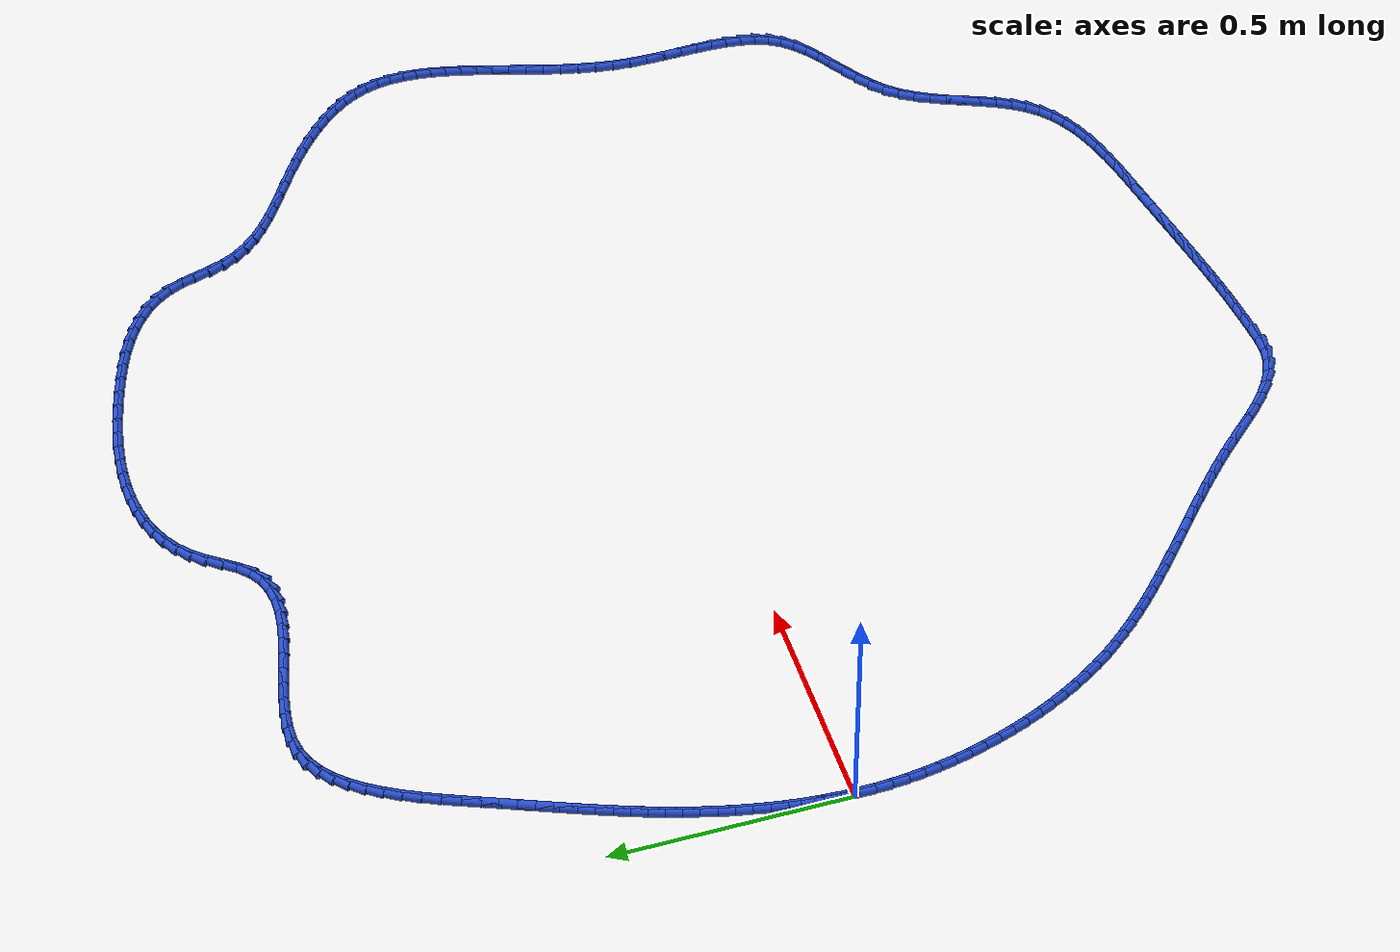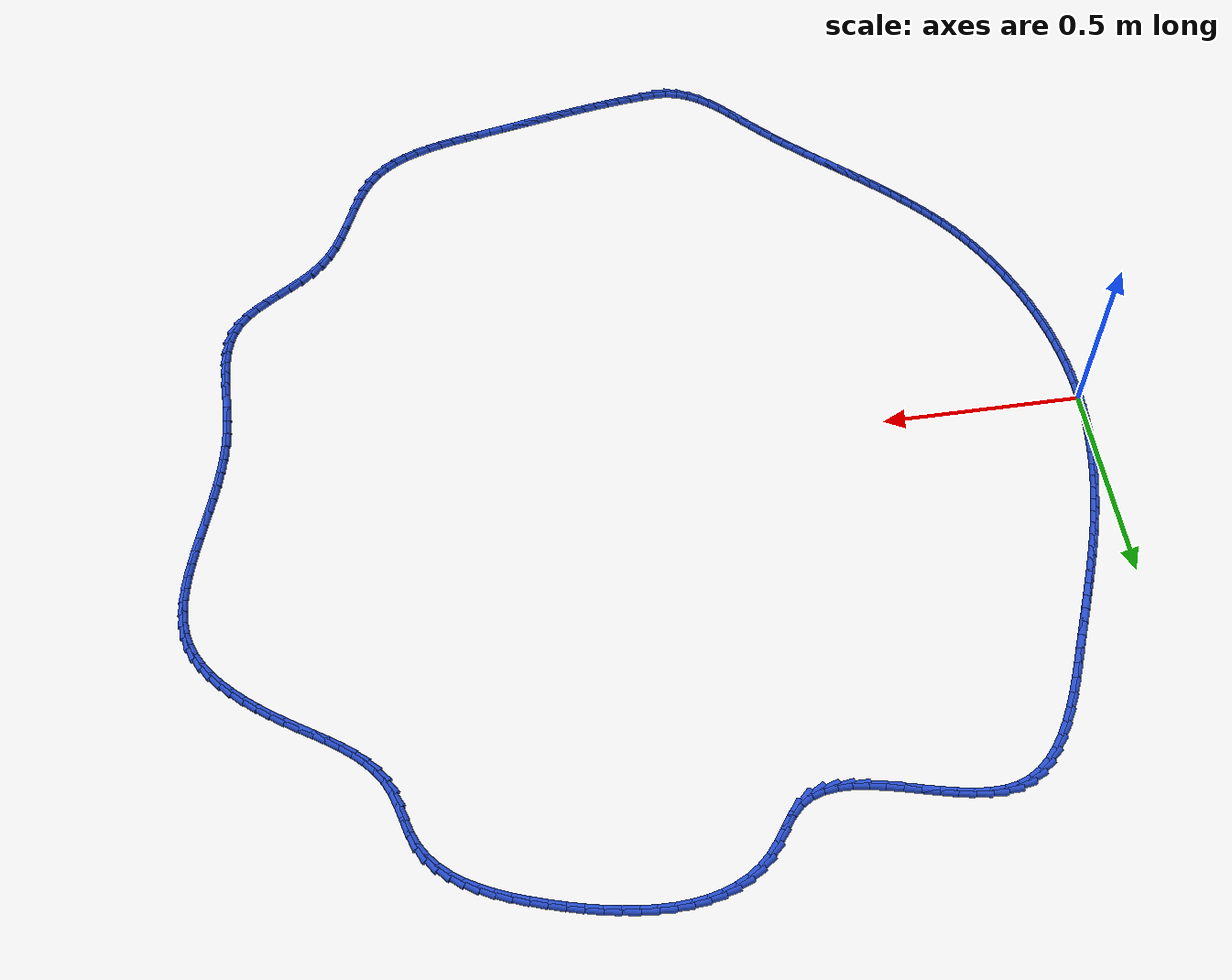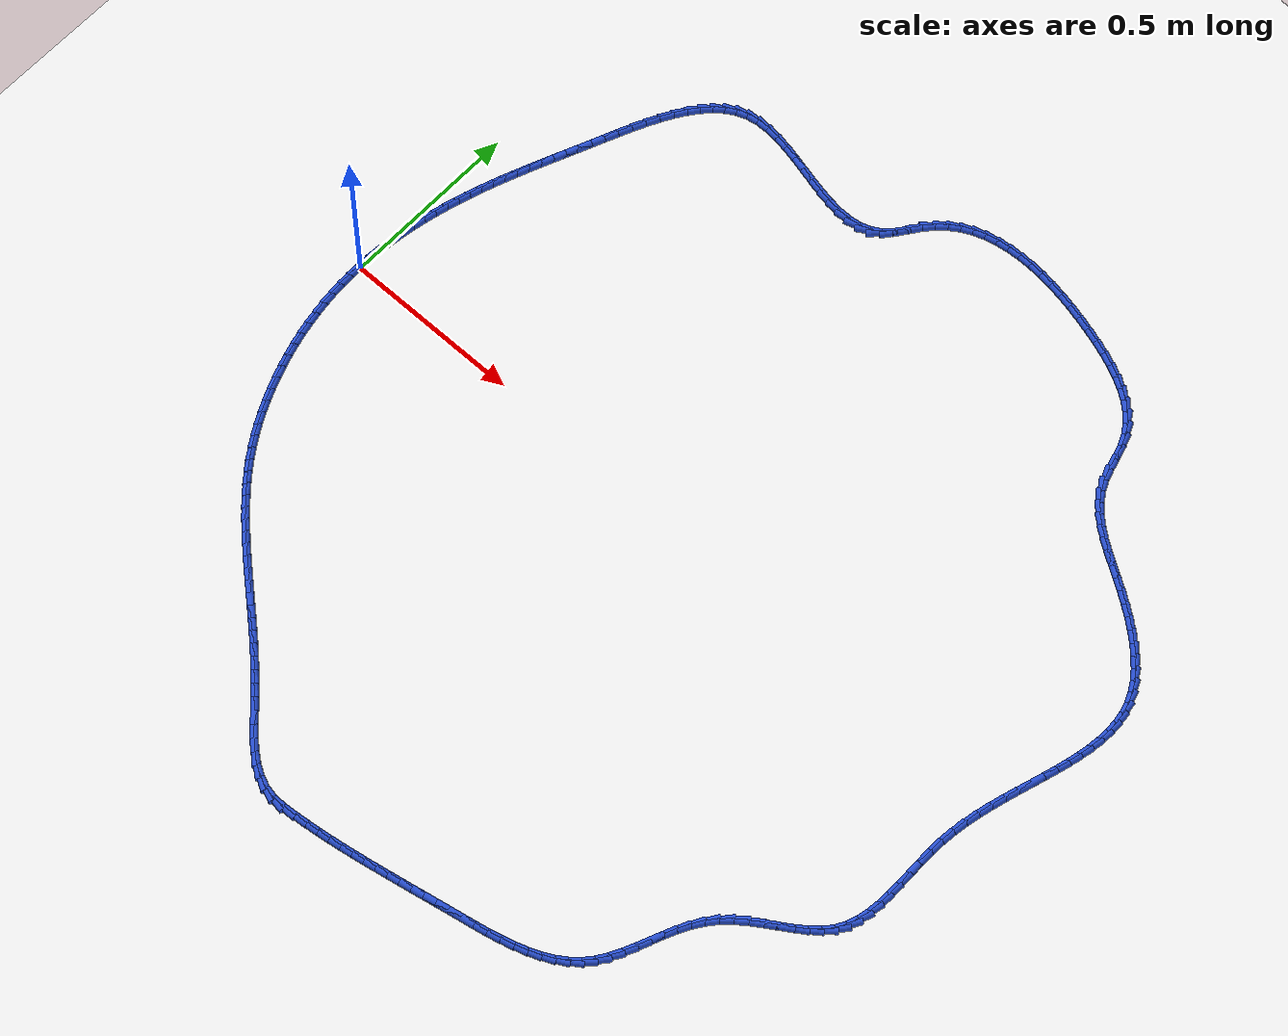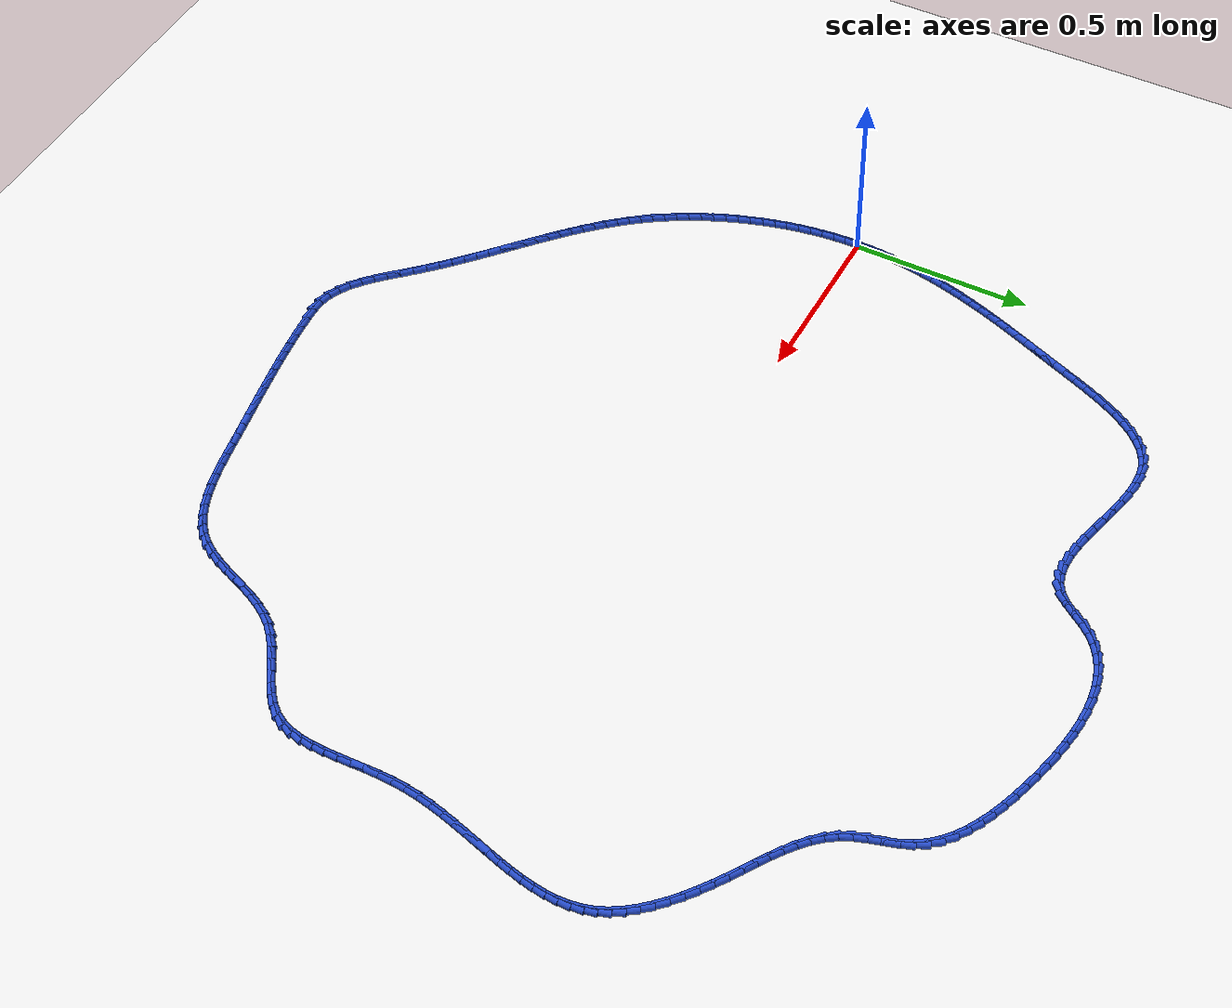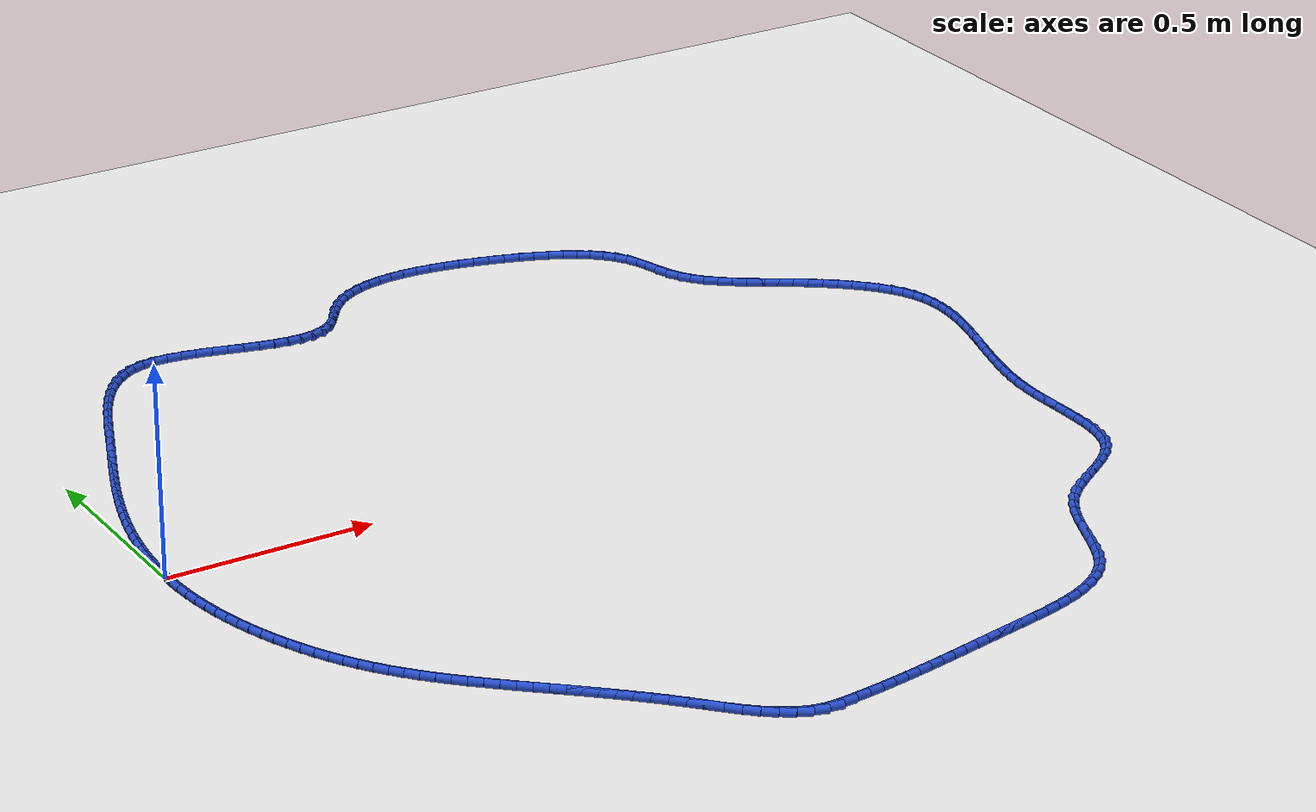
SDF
<sdf version="1.6">
 <world name="default">
  <light name="sun" type="directional">
   <pose>0 0 10 0 -0 0</pose>
   <diffuse>0.8 0.8 0.8 1</diffuse>
   <specular>0.2 0.2 0.2 1</specular>
   <attenuation>
    <range>1000</range>
    <constant>0.9</constant>
    <linear>0.01</linear>
    <quadratic>0.001</quadratic>
   </attenuation>
   <direction>-0.5 0.1 -0.9</direction>
  </light>
  <model name="ground_plane">
   <static>1</static>
   <link name="link">
    <collision name="collision">
     <geometry><plane><normal>0 0 1</normal><size>100 100</size></plane></geometry>
     <surface><friction><ode><mu>100</mu><mu2>50</mu2></ode></friction></surface>
    </collision>
    <visual name="visual">
     <cast_shadows>0</cast_shadows>
     <geometry><plane><normal>0 0 1</normal><size>100 100</size></plane></geometry>
     <material>
      <script><uri>file://media/materials/scripts/gazebo.material</uri><name>Gazebo/WhiteGlow</name></script>
     </material>
    </visual>
   </link>
  </model>
  <gravity>0 0 -9.8</gravity>
  <magnetic_field>6e-06 2.3e-05 -4.2e-05</magnetic_field>
  <atmosphere type="adiabatic"/>
  <physics name="default_physics" default="0" type="ode">
   <max_step_size>0.001</max_step_size>
   <real_time_factor>1</real_time_factor>
   <real_time_update_rate>1000</real_time_update_rate>
  </physics>
  <scene><ambient>0.4 0.4 0.4 1</ambient><background>0.7 0.7 0.7 1</background><shadows>1</shadows></scene>
  <spherical_coordinates>
   <surface_model>EARTH_WGS84</surface_model>
   <latitude_deg>0</latitude_deg>
   <longitude_deg>0</longitude_deg>
   <elevation>0</elevation>
   <heading_deg>0</heading_deg>
  </spherical_coordinates>
  <model name="line">
   <link name="link_0">
    <pose>-3.469446951953614e-18 -9.020562075079397e-17 0.01 0 1.57 1.5426617681742363</pose>
    <collision name="collision">
     <geometry><cylinder><radius>0.01</radius><length>0.08</length></cylinder></geometry>
    </collision>
    <visual name="visual">
     <material>
      <script><name>Gazebo/Blue</name><uri>file://media/materials/scripts/gazebo.material</uri></script>
     </material>
     <geometry><cylinder><radius>0.01</radius><length>0.08</length></cylinder></geometry>
    </visual>
   </link>
   <link name="link_1">
    <pose>0.0009700444120622061 0.03446965222794556 0.01 0 1.57 1.5068231964550598</pose>
    <collision name="collision">
     <geometry><cylinder><radius>0.01</radius><length>0.08</length></cylinder></geometry>
    </collision>
    <visual name="visual">
     <material>
      <script><name>Gazebo/Blue</name><uri>file://media/materials/scripts/gazebo.material</uri></script>
     </material>
     <geometry><cylinder><radius>0.01</radius><length>0.08</length></cylinder></geometry>
    </visual>
   </link>
   <link name="link_2">
    <pose>0.0031786117746234596 0.06894590232403473 0.01 0 1.57 1.4730845369021786</pose>
    <collision name="collision">
     <geometry><cylinder><radius>0.01</radius><length>0.08</length></cylinder></geometry>
    </collision>
    <visual name="visual">
     <material>
      <script><name>Gazebo/Blue</name><uri>file://media/materials/scripts/gazebo.material</uri></script>
     </material>
     <geometry><cylinder><radius>0.01</radius><length>0.08</length></cylinder></geometry>
    </visual>
   </link>
   <link name="link_3">
    <pose>0.006551479913786688 0.1033545140771062 0.01 0 1.57 1.441283973052966</pose>
    <collision name="collision">
     <geometry><cylinder><radius>0.01</radius><length>0.08</length></cylinder></geometry>
    </collision>
    <visual name="visual">
     <material>
      <script><name>Gazebo/Blue</name><uri>file://media/materials/scripts/gazebo.material</uri></script>
     </material>
     <geometry><cylinder><radius>0.01</radius><length>0.08</length></cylinder></geometry>
    </visual>
   </link>
   <link name="link_4">
    <pose>0.011014426655654807 0.13762125127599864 0.01 0 1.57 1.4112620103847309</pose>
    <collision name="collision">
     <geometry><cylinder><radius>0.01</radius><length>0.08</length></cylinder></geometry>
    </collision>
    <visual name="visual">
     <material>
      <script><name>Gazebo/Blue</name><uri>file://media/materials/scripts/gazebo.material</uri></script>
     </material>
     <geometry><cylinder><radius>0.01</radius><length>0.08</length></cylinder></geometry>
    </visual>
   </link>
   <link name="link_5">
    <pose>0.016493229826330752 0.1716718777095508 0.01 0 1.57 1.3828633024975148</pose>
    <collision name="collision">
     <geometry><cylinder><radius>0.01</radius><length>0.08</length></cylinder></geometry>
    </collision>
    <visual name="visual">
     <material>
      <script><name>Gazebo/Blue</name><uri>file://media/materials/scripts/gazebo.material</uri></script>
     </material>
     <geometry><cylinder><radius>0.01</radius><length>0.08</length></cylinder></geometry>
    </visual>
   </link>
   <link name="link_6">
    <pose>0.022913667251917458 0.20543215716660157 0.01 0 1.57 1.3559376009215622</pose>
    <collision name="collision">
     <geometry><cylinder><radius>0.01</radius><length>0.08</length></cylinder></geometry>
    </collision>
    <visual name="visual">
     <material>
      <script><name>Gazebo/Blue</name><uri>file://media/materials/scripts/gazebo.material</uri></script>
     </material>
     <geometry><cylinder><radius>0.01</radius><length>0.08</length></cylinder></geometry>
    </visual>
   </link>
   <link name="link_7">
    <pose>0.03020151675851784 0.23882785343598956 0.01 0 1.57 1.3303400099889016</pose>
    <collision name="collision">
     <geometry><cylinder><radius>0.01</radius><length>0.08</length></cylinder></geometry>
    </collision>
    <visual name="visual">
     <material>
      <script><name>Gazebo/Blue</name><uri>file://media/materials/scripts/gazebo.material</uri></script>
     </material>
     <geometry><cylinder><radius>0.01</radius><length>0.08</length></cylinder></geometry>
    </visual>
   </link>
   <link name="link_8">
    <pose>0.03828255617223482 0.27178473030655337 0.01 0 1.57 1.3059326749395184</pose>
    <collision name="collision">
     <geometry><cylinder><radius>0.01</radius><length>0.08</length></cylinder></geometry>
    </collision>
    <visual name="visual">
     <material>
      <script><name>Gazebo/Blue</name><uri>file://media/materials/scripts/gazebo.material</uri></script>
     </material>
     <geometry><cylinder><radius>0.01</radius><length>0.08</length></cylinder></geometry>
    </visual>
   </link>
   <link name="link_9">
    <pose>0.047082728457098454 0.3042294160180554 0.01 0 1.57 1.2827956050872755</pose>
    <collision name="collision">
     <geometry><cylinder><radius>0.01</radius><length>0.08</length></cylinder></geometry>
    </collision>
    <visual name="visual">
     <material>
      <script><name>Gazebo/Blue</name><uri>file://media/materials/scripts/gazebo.material</uri></script>
     </material>
     <geometry><cylinder><radius>0.01</radius><length>0.08</length></cylinder></geometry>
    </visual>
   </link>
   <link name="link_10">
    <pose>0.056541421908028675 0.33615892136201503 0.01 0 1.57 1.2614004162500048</pose>
    <collision name="collision">
     <geometry><cylinder><radius>0.01</radius><length>0.08</length></cylinder></geometry>
    </collision>
    <visual name="visual">
     <material>
      <script><name>Gazebo/Blue</name><uri>file://media/materials/scripts/gazebo.material</uri></script>
     </material>
     <geometry><cylinder><radius>0.01</radius><length>0.08</length></cylinder></geometry>
    </visual>
   </link>
   <link name="link_11">
    <pose>0.06662120237509289 0.3676915851573642 0.01 0 1.57 1.2420481661888583</pose>
    <collision name="collision">
     <geometry><cylinder><radius>0.01</radius><length>0.08</length></cylinder></geometry>
    </collision>
    <visual name="visual">
     <material>
      <script><name>Gazebo/Blue</name><uri>file://media/materials/scripts/gazebo.material</uri></script>
     </material>
     <geometry><cylinder><radius>0.01</radius><length>0.08</length></cylinder></geometry>
    </visual>
   </link>
   <link name="link_12">
    <pose>0.0772869301197786 0.39895775682596096 0.01 0 1.57 1.224964220346381</pose>
    <collision name="collision">
     <geometry><cylinder><radius>0.01</radius><length>0.08</length></cylinder></geometry>
    </collision>
    <visual name="visual">
     <material>
      <script><name>Gazebo/Blue</name><uri>file://media/materials/scripts/gazebo.material</uri></script>
     </material>
     <geometry><cylinder><radius>0.01</radius><length>0.08</length></cylinder></geometry>
    </visual>
   </link>
   <link name="link_13">
    <pose>0.08850346540357334 0.4300877857896637 0.01 0 1.57 1.2103193462445507</pose>
    <collision name="collision">
     <geometry><cylinder><radius>0.01</radius><length>0.08</length></cylinder></geometry>
    </collision>
    <visual name="visual">
     <material>
      <script><name>Gazebo/Blue</name><uri>file://media/materials/scripts/gazebo.material</uri></script>
     </material>
     <geometry><cylinder><radius>0.01</radius><length>0.08</length></cylinder></geometry>
    </visual>
   </link>
   <link name="link_14">
    <pose>0.10023566848796471 0.46121202147033075 0.01 0 1.57 1.1982265323540588</pose>
    <collision name="collision">
     <geometry><cylinder><radius>0.01</radius><length>0.08</length></cylinder></geometry>
    </collision>
    <visual name="visual">
     <material>
      <script><name>Gazebo/Blue</name><uri>file://media/materials/scripts/gazebo.material</uri></script>
     </material>
     <geometry><cylinder><radius>0.01</radius><length>0.08</length></cylinder></geometry>
    </visual>
   </link>
   <link name="link_15">
    <pose>0.11244839963444016 0.49246081328982 0.01 0 1.57 1.188740996866804</pose>
    <collision name="collision">
     <geometry><cylinder><radius>0.01</radius><length>0.08</length></cylinder></geometry>
    </collision>
    <visual name="visual">
     <material>
      <script><name>Gazebo/Blue</name><uri>file://media/materials/scripts/gazebo.material</uri></script>
     </material>
     <geometry><cylinder><radius>0.01</radius><length>0.08</length></cylinder></geometry>
    </visual>
   </link>
   <link name="link_16">
    <pose>0.12510651910448728 0.5239645106699898 0.01 0 1.57 1.1818629321906435</pose>
    <collision name="collision">
     <geometry><cylinder><radius>0.01</radius><length>0.08</length></cylinder></geometry>
    </collision>
    <visual name="visual">
     <material>
      <script><name>Gazebo/Blue</name><uri>file://media/materials/scripts/gazebo.material</uri></script>
     </material>
     <geometry><cylinder><radius>0.01</radius><length>0.08</length></cylinder></geometry>
    </visual>
   </link>
   <link name="link_17">
    <pose>0.13817488715959353 0.5558534630326982 0.01 0 1.57 1.1775423774596836</pose>
    <collision name="collision">
     <geometry><cylinder><radius>0.01</radius><length>0.08</length></cylinder></geometry>
    </collision>
    <visual name="visual">
     <material>
      <script><name>Gazebo/Blue</name><uri>file://media/materials/scripts/gazebo.material</uri></script>
     </material>
     <geometry><cylinder><radius>0.01</radius><length>0.08</length></cylinder></geometry>
    </visual>
   </link>
   <link name="link_18">
    <pose>0.1516183640612465 0.5882580197998035 0.01 0 1.57 1.1756855686879841</pose>
    <collision name="collision">
     <geometry><cylinder><radius>0.01</radius><length>0.08</length></cylinder></geometry>
    </collision>
    <visual name="visual">
     <material>
      <script><name>Gazebo/Blue</name><uri>file://media/materials/scripts/gazebo.material</uri></script>
     </material>
     <geometry><cylinder><radius>0.01</radius><length>0.08</length></cylinder></geometry>
    </visual>
   </link>
   <link name="link_19">
    <pose>0.16540181007093377 0.621308530393164 0.01 0 1.57 1.1761621559635473</pose>
    <collision name="collision">
     <geometry><cylinder><radius>0.01</radius><length>0.08</length></cylinder></geometry>
    </collision>
    <visual name="visual">
     <material>
      <script><name>Gazebo/Blue</name><uri>file://media/materials/scripts/gazebo.material</uri></script>
     </material>
     <geometry><cylinder><radius>0.01</radius><length>0.08</length></cylinder></geometry>
    </visual>
   </link>
   <link name="link_20">
    <pose>0.17949008545014275 0.6551353442346376 0.01 0 1.57 1.1786547158440774</pose>
    <collision name="collision">
     <geometry><cylinder><radius>0.01</radius><length>0.08</length></cylinder></geometry>
    </collision>
    <visual name="visual">
     <material>
      <script><name>Gazebo/Blue</name><uri>file://media/materials/scripts/gazebo.material</uri></script>
     </material>
     <geometry><cylinder><radius>0.01</radius><length>0.08</length></cylinder></geometry>
    </visual>
   </link>
   <link name="link_21">
    <pose>0.19385090474960048 0.6898601692216936 0.01 0 1.57 1.1775593518212568</pose>
    <collision name="collision">
     <geometry><cylinder><radius>0.01</radius><length>0.08</length></cylinder></geometry>
    </collision>
    <visual name="visual">
     <material>
      <script><name>Gazebo/Blue</name><uri>file://media/materials/scripts/gazebo.material</uri></script>
     </material>
     <geometry><cylinder><radius>0.01</radius><length>0.08</length></cylinder></geometry>
    </visual>
   </link>
   <link name="link_22">
    <pose>0.20855274997165604 0.7252996340121879 0.01 0 1.57 1.1663037624099122</pose>
    <collision name="collision">
     <geometry><cylinder><radius>0.01</radius><length>0.08</length></cylinder></geometry>
    </collision>
    <visual name="visual">
     <material>
      <script><name>Gazebo/Blue</name><uri>file://media/materials/scripts/gazebo.material</uri></script>
     </material>
     <geometry><cylinder><radius>0.01</radius><length>0.08</length></cylinder></geometry>
    </visual>
   </link>
   <link name="link_23">
    <pose>0.22378939431533637 0.7608910409795715 0.01 0 1.57 1.1443427767224301</pose>
    <collision name="collision">
     <geometry><cylinder><radius>0.01</radius><length>0.08</length></cylinder></geometry>
    </collision>
    <visual name="visual">
     <material>
      <script><name>Gazebo/Blue</name><uri>file://media/materials/scripts/gazebo.material</uri></script>
     </material>
     <geometry><cylinder><radius>0.01</radius><length>0.08</length></cylinder></geometry>
    </visual>
   </link>
   <link name="link_24">
    <pose>0.23976244308564343 0.7960479803472201 0.01 0 1.57 1.1108342289105209</pose>
    <collision name="collision">
     <geometry><cylinder><radius>0.01</radius><length>0.08</length></cylinder></geometry>
    </collision>
    <visual name="visual">
     <material>
      <script><name>Gazebo/Blue</name><uri>file://media/materials/scripts/gazebo.material</uri></script>
     </material>
     <geometry><cylinder><radius>0.01</radius><length>0.08</length></cylinder></geometry>
    </visual>
   </link>
   <link name="link_25">
    <pose>0.2566735015875796 0.8301840423385108 0.01 0 1.57 1.0641881782192404</pose>
    <collision name="collision">
     <geometry><cylinder><radius>0.01</radius><length>0.08</length></cylinder></geometry>
    </collision>
    <visual name="visual">
     <material>
      <script><name>Gazebo/Blue</name><uri>file://media/materials/scripts/gazebo.material</uri></script>
     </material>
     <geometry><cylinder><radius>0.01</radius><length>0.08</length></cylinder></geometry>
    </visual>
   </link>
   <link name="link_26">
    <pose>0.2747241751261469 0.8627128171768198 0.01 0 1.57 1.0020108116715092</pose>
    <collision name="collision">
     <geometry><cylinder><radius>0.01</radius><length>0.08</length></cylinder></geometry>
    </collision>
    <visual name="visual">
     <material>
      <script><name>Gazebo/Blue</name><uri>file://media/materials/scripts/gazebo.material</uri></script>
     </material>
     <geometry><cylinder><radius>0.01</radius><length>0.08</length></cylinder></geometry>
    </visual>
   </link>
   <link name="link_27">
    <pose>0.29411606900634746 0.8930478950855231 0.01 0 1.57 0.9210882730769017</pose>
    <collision name="collision">
     <geometry><cylinder><radius>0.01</radius><length>0.08</length></cylinder></geometry>
    </collision>
    <visual name="visual">
     <material>
      <script><name>Gazebo/Blue</name><uri>file://media/materials/scripts/gazebo.material</uri></script>
     </material>
     <geometry><cylinder><radius>0.01</radius><length>0.08</length></cylinder></geometry>
    </visual>
   </link>
   <link name="link_28">
    <pose>0.3150507885331837 0.9206028662879975 0.01 0 1.57 0.8175906086443833</pose>
    <collision name="collision">
     <geometry><cylinder><radius>0.01</radius><length>0.08</length></cylinder></geometry>
    </collision>
    <visual name="visual">
     <material>
      <script><name>Gazebo/Blue</name><uri>file://media/materials/scripts/gazebo.material</uri></script>
     </material>
     <geometry><cylinder><radius>0.01</radius><length>0.08</length></cylinder></geometry>
    </visual>
   </link>
   <link name="link_29">
    <pose>0.3377299390116573 0.9447913210076189 0.01 0 1.57 0.6878578503736322</pose>
    <collision name="collision">
     <geometry><cylinder><radius>0.01</radius><length>0.08</length></cylinder></geometry>
    </collision>
    <visual name="visual">
     <material>
      <script><name>Gazebo/Blue</name><uri>file://media/materials/scripts/gazebo.material</uri></script>
     </material>
     <geometry><cylinder><radius>0.01</radius><length>0.08</length></cylinder></geometry>
    </visual>
   </link>
   <link name="link_30">
    <pose>0.3623551257467708 0.965026849467764 0.01 0 1.57 0.5302651371534446</pose>
    <collision name="collision">
     <geometry><cylinder><radius>0.01</radius><length>0.08</length></cylinder></geometry>
    </collision>
    <visual name="visual">
     <material>
      <script><name>Gazebo/Blue</name><uri>file://media/materials/scripts/gazebo.material</uri></script>
     </material>
     <geometry><cylinder><radius>0.01</radius><length>0.08</length></cylinder></geometry>
    </visual>
   </link>
   <link name="link_31">
    <pose>0.3891279540435262 0.980723041891809 0.01 0 1.57 0.34818254958315464</pose>
    <collision name="collision">
     <geometry><cylinder><radius>0.01</radius><length>0.08</length></cylinder></geometry>
    </collision>
    <visual name="visual">
     <material>
      <script><name>Gazebo/Blue</name><uri>file://media/materials/scripts/gazebo.material</uri></script>
     </material>
     <geometry><cylinder><radius>0.01</radius><length>0.08</length></cylinder></geometry>
    </visual>
   </link>
   <link name="link_32">
    <pose>0.41825002920692567 0.9912934885031303 0.01 0 1.57 0.16001263623155992</pose>
    <collision name="collision">
     <geometry><cylinder><radius>0.01</radius><length>0.08</length></cylinder></geometry>
    </collision>
    <visual name="visual">
     <material>
      <script><name>Gazebo/Blue</name><uri>file://media/materials/scripts/gazebo.material</uri></script>
     </material>
     <geometry><cylinder><radius>0.01</radius><length>0.08</length></cylinder></geometry>
    </visual>
   </link>
   <link name="link_33">
    <pose>0.4498248670189138 0.9963894281807768 0.01 0 1.57 0.008466774421123499</pose>
    <collision name="collision">
     <geometry><cylinder><radius>0.01</radius><length>0.08</length></cylinder></geometry>
    </collision>
    <visual name="visual">
     <material>
      <script><name>Gazebo/Blue</name><uri>file://media/materials/scripts/gazebo.material</uri></script>
     </material>
     <geometry><cylinder><radius>0.01</radius><length>0.08</length></cylinder></geometry>
    </visual>
   </link>
   <link name="link_34">
    <pose>0.4835379596513926 0.9966748761520671 0.01 0 1.57 -0.1010305521893574</pose>
    <collision name="collision">
     <geometry><cylinder><radius>0.01</radius><length>0.08</length></cylinder></geometry>
    </collision>
    <visual name="visual">
     <material>
      <script><name>Gazebo/Blue</name><uri>file://media/materials/scripts/gazebo.material</uri></script>
     </material>
     <geometry><cylinder><radius>0.01</radius><length>0.08</length></cylinder></geometry>
    </visual>
   </link>
   <link name="link_35">
    <pose>0.5189634627714 0.9930835907308748 0.01 0 1.57 -0.17614209295042063</pose>
    <collision name="collision">
     <geometry><cylinder><radius>0.01</radius><length>0.08</length></cylinder></geometry>
    </collision>
    <visual name="visual">
     <material>
      <script><name>Gazebo/Blue</name><uri>file://media/materials/scripts/gazebo.material</uri></script>
     </material>
     <geometry><cylinder><radius>0.01</radius><length>0.08</length></cylinder></geometry>
    </visual>
   </link>
   <link name="link_36">
    <pose>0.5556755310614322 0.9865493326163968 0.01 0 1.57 -0.2235828932018794</pose>
    <collision name="collision">
     <geometry><cylinder><radius>0.01</radius><length>0.08</length></cylinder></geometry>
    </collision>
    <visual name="visual">
     <material>
      <script><name>Gazebo/Blue</name><uri>file://media/materials/scripts/gazebo.material</uri></script>
     </material>
     <geometry><cylinder><radius>0.01</radius><length>0.08</length></cylinder></geometry>
    </visual>
   </link>
   <link name="link_37">
    <pose>0.5932483192039847 0.9780058625078278 0.01 0 1.57 -0.2478739484184134</pose>
    <collision name="collision">
     <geometry><cylinder><radius>0.01</radius><length>0.08</length></cylinder></geometry>
    </collision>
    <visual name="visual">
     <material>
      <script><name>Gazebo/Blue</name><uri>file://media/materials/scripts/gazebo.material</uri></script>
     </material>
     <geometry><cylinder><radius>0.01</radius><length>0.08</length></cylinder></geometry>
    </visual>
   </link>
   <link name="link_38">
    <pose>0.6312559818815534 0.9683869411043635 0.01 0 1.57 -0.25131716015431266</pose>
    <collision name="collision">
     <geometry><cylinder><radius>0.01</radius><length>0.08</length></cylinder></geometry>
    </collision>
    <visual name="visual">
     <material>
      <script><name>Gazebo/Blue</name><uri>file://media/materials/scripts/gazebo.material</uri></script>
     </material>
     <geometry><cylinder><radius>0.01</radius><length>0.08</length></cylinder></geometry>
    </visual>
   </link>
   <link name="link_39">
    <pose>0.6692726737766346 0.9586263291052 0.01 0 1.57 -0.23415064069050673</pose>
    <collision name="collision">
     <geometry><cylinder><radius>0.01</radius><length>0.08</length></cylinder></geometry>
    </collision>
    <visual name="visual">
     <material>
      <script><name>Gazebo/Blue</name><uri>file://media/materials/scripts/gazebo.material</uri></script>
     </material>
     <geometry><cylinder><radius>0.01</radius><length>0.08</length></cylinder></geometry>
    </visual>
   </link>
   <link name="link_40">
    <pose>0.7068725495717239 0.949657787209532 0.01 0 1.57 -0.194549614665824</pose>
    <collision name="collision">
     <geometry><cylinder><radius>0.01</radius><length>0.08</length></cylinder></geometry>
    </collision>
    <visual name="visual">
     <material>
      <script><name>Gazebo/Blue</name><uri>file://media/materials/scripts/gazebo.material</uri></script>
     </material>
     <geometry><cylinder><radius>0.01</radius><length>0.08</length></cylinder></geometry>
    </visual>
   </link>
   <link name="link_41">
    <pose>0.7436297639493172 0.9424150761165558 0.01 0 1.57 -0.12843219386284946</pose>
    <collision name="collision">
     <geometry><cylinder><radius>0.01</radius><length>0.08</length></cylinder></geometry>
    </collision>
    <visual name="visual">
     <material>
      <script><name>Gazebo/Blue</name><uri>file://media/materials/scripts/gazebo.material</uri></script>
     </material>
     <geometry><cylinder><radius>0.01</radius><length>0.08</length></cylinder></geometry>
    </visual>
   </link>
   <link name="link_42">
    <pose>0.7791184715919108 0.937831956525467 0.01 0 1.57 -0.029279579861216275</pose>
    <collision name="collision">
     <geometry><cylinder><radius>0.01</radius><length>0.08</length></cylinder></geometry>
    </collision>
    <visual name="visual">
     <material>
      <script><name>Gazebo/Blue</name><uri>file://media/materials/scripts/gazebo.material</uri></script>
     </material>
     <geometry><cylinder><radius>0.01</radius><length>0.08</length></cylinder></geometry>
    </visual>
   </link>
   <link name="link_43">
    <pose>0.8129128271820006 0.9368421891354609 0.01 0 1.57 0.11121837390763155</pose>
    <collision name="collision">
     <geometry><cylinder><radius>0.01</radius><length>0.08</length></cylinder></geometry>
    </collision>
    <visual name="visual">
     <material>
      <script><name>Gazebo/Blue</name><uri>file://media/materials/scripts/gazebo.material</uri></script>
     </material>
     <geometry><cylinder><radius>0.01</radius><length>0.08</length></cylinder></geometry>
    </visual>
   </link>
   <link name="link_44">
    <pose>0.8445869854020821 0.9403795346457331 0.01 0 1.57 0.29961885614698375</pose>
    <collision name="collision">
     <geometry><cylinder><radius>0.01</radius><length>0.08</length></cylinder></geometry>
    </collision>
    <visual name="visual">
     <material>
      <script><name>Gazebo/Blue</name><uri>file://media/materials/scripts/gazebo.material</uri></script>
     </material>
     <geometry><cylinder><radius>0.01</radius><length>0.08</length></cylinder></geometry>
    </visual>
   </link>
   <link name="link_45">
    <pose>0.8737151009346513 0.9493777537554791 0.01 0 1.57 0.5319182465018285</pose>
    <collision name="collision">
     <geometry><cylinder><radius>0.01</radius><length>0.08</length></cylinder></geometry>
    </collision>
    <visual name="visual">
     <material>
      <script><name>Gazebo/Blue</name><uri>file://media/materials/scripts/gazebo.material</uri></script>
     </material>
     <geometry><cylinder><radius>0.01</radius><length>0.08</length></cylinder></geometry>
    </visual>
   </link>
   <link name="link_46">
    <pose>0.8998713284622049 0.9647706071638951 0.01 0 1.57 0.774930430798748</pose>
    <collision name="collision">
     <geometry><cylinder><radius>0.01</radius><length>0.08</length></cylinder></geometry>
    </collision>
    <visual name="visual">
     <material>
      <script><name>Gazebo/Blue</name><uri>file://media/materials/scripts/gazebo.material</uri></script>
     </material>
     <geometry><cylinder><radius>0.01</radius><length>0.08</length></cylinder></geometry>
    </visual>
   </link>
   <link name="link_47">
    <pose>0.9227779407021346 0.9872026095742683 0.01 0 1.57 0.9207620130363051</pose>
    <collision name="collision">
     <geometry><cylinder><radius>0.01</radius><length>0.08</length></cylinder></geometry>
    </collision>
    <visual name="visual">
     <material>
      <script><name>Gazebo/Blue</name><uri>file://media/materials/scripts/gazebo.material</uri></script>
     </material>
     <geometry><cylinder><radius>0.01</radius><length>0.08</length></cylinder></geometry>
    </visual>
   </link>
   <link name="link_48">
    <pose>0.9435724757292667 1.0145545350146317 0.01 0 1.57 0.946753013525226</pose>
    <collision name="collision">
     <geometry><cylinder><radius>0.01</radius><length>0.08</length></cylinder></geometry>
    </collision>
    <visual name="visual">
     <material>
      <script><name>Gazebo/Blue</name><uri>file://media/materials/scripts/gazebo.material</uri></script>
     </material>
     <geometry><cylinder><radius>0.01</radius><length>0.08</length></cylinder></geometry>
    </visual>
   </link>
   <link name="link_49">
    <pose>0.9641783219672696 1.043172543129673 0.01 0 1.57 0.8669294178932866</pose>
    <collision name="collision">
     <geometry><cylinder><radius>0.01</radius><length>0.08</length></cylinder></geometry>
    </collision>
    <visual name="visual">
     <material>
      <script><name>Gazebo/Blue</name><uri>file://media/materials/scripts/gazebo.material</uri></script>
     </material>
     <geometry><cylinder><radius>0.01</radius><length>0.08</length></cylinder></geometry>
    </visual>
   </link>
   <link name="link_50">
    <pose>0.9864895327444952 1.0694544105416728 0.01 0 1.57 0.7266920355072394</pose>
    <collision name="collision">
     <geometry><cylinder><radius>0.01</radius><length>0.08</length></cylinder></geometry>
    </collision>
    <visual name="visual">
     <material>
      <script><name>Gazebo/Blue</name><uri>file://media/materials/scripts/gazebo.material</uri></script>
     </material>
     <geometry><cylinder><radius>0.01</radius><length>0.08</length></cylinder></geometry>
    </visual>
   </link>
   <link name="link_51">
    <pose>1.0114005778594204 1.0915997779362427 0.01 0 1.57 0.5863528986662768</pose>
    <collision name="collision">
     <geometry><cylinder><radius>0.01</radius><length>0.08</length></cylinder></geometry>
    </collision>
    <visual name="visual">
     <material>
      <script><name>Gazebo/Blue</name><uri>file://media/materials/scripts/gazebo.material</uri></script>
     </material>
     <geometry><cylinder><radius>0.01</radius><length>0.08</length></cylinder></geometry>
    </visual>
   </link>
   <link name="link_52">
    <pose>1.0387273356943583 1.1097525708473537 0.01 0 1.57 0.454066939665086</pose>
    <collision name="collision">
     <geometry><cylinder><radius>0.01</radius><length>0.08</length></cylinder></geometry>
    </collision>
    <visual name="visual">
     <material>
      <script><name>Gazebo/Blue</name><uri>file://media/materials/scripts/gazebo.material</uri></script>
     </material>
     <geometry><cylinder><radius>0.01</radius><length>0.08</length></cylinder></geometry>
    </visual>
   </link>
   <link name="link_53">
    <pose>1.0682321107557462 1.1241532878704417 0.01 0 1.57 0.3333663685246123</pose>
    <collision name="collision">
     <geometry><cylinder><radius>0.01</radius><length>0.08</length></cylinder></geometry>
    </collision>
    <visual name="visual">
     <material>
      <script><name>Gazebo/Blue</name><uri>file://media/materials/scripts/gazebo.material</uri></script>
     </material>
     <geometry><cylinder><radius>0.01</radius><length>0.08</length></cylinder></geometry>
    </visual>
   </link>
   <link name="link_54">
    <pose>1.099677207550022 1.1350424276009448 0.01 0 1.57 0.22589889558265125</pose>
    <collision name="collision">
     <geometry><cylinder><radius>0.01</radius><length>0.08</length></cylinder></geometry>
    </collision>
    <visual name="visual">
     <material>
      <script><name>Gazebo/Blue</name><uri>file://media/materials/scripts/gazebo.material</uri></script>
     </material>
     <geometry><cylinder><radius>0.01</radius><length>0.08</length></cylinder></geometry>
    </visual>
   </link>
   <link name="link_55">
    <pose>1.1328249305836235 1.1426604886343 0.01 0 1.57 0.1317696983734423</pose>
    <collision name="collision">
     <geometry><cylinder><radius>0.01</radius><length>0.08</length></cylinder></geometry>
    </collision>
    <visual name="visual">
     <material>
      <script><name>Gazebo/Blue</name><uri>file://media/materials/scripts/gazebo.material</uri></script>
     </material>
     <geometry><cylinder><radius>0.01</radius><length>0.08</length></cylinder></geometry>
    </visual>
   </link>
   <link name="link_56">
    <pose>1.1674375843629894 1.1472479695659443 0.01 0 1.57 0.05010882739480579</pose>
    <collision name="collision">
     <geometry><cylinder><radius>0.01</radius><length>0.08</length></cylinder></geometry>
    </collision>
    <visual name="visual">
     <material>
      <script><name>Gazebo/Blue</name><uri>file://media/materials/scripts/gazebo.material</uri></script>
     </material>
     <geometry><cylinder><radius>0.01</radius><length>0.08</length></cylinder></geometry>
    </visual>
   </link>
   <link name="link_57">
    <pose>1.2032774733945566 1.1490453689913158 0.01 0 1.57 -0.02042059715724036</pose>
    <collision name="collision">
     <geometry><cylinder><radius>0.01</radius><length>0.08</length></cylinder></geometry>
    </collision>
    <visual name="visual">
     <material>
      <script><name>Gazebo/Blue</name><uri>file://media/materials/scripts/gazebo.material</uri></script>
     </material>
     <geometry><cylinder><radius>0.01</radius><length>0.08</length></cylinder></geometry>
    </visual>
   </link>
   <link name="link_58">
    <pose>1.240106902184763 1.148293185505851 0.01 0 1.57 -0.08127781698062835</pose>
    <collision name="collision">
     <geometry><cylinder><radius>0.01</radius><length>0.08</length></cylinder></geometry>
    </collision>
    <visual name="visual">
     <material>
      <script><name>Gazebo/Blue</name><uri>file://media/materials/scripts/gazebo.material</uri></script>
     </material>
     <geometry><cylinder><radius>0.01</radius><length>0.08</length></cylinder></geometry>
    </visual>
   </link>
   <link name="link_59">
    <pose>1.2776881752400464 1.1452319177049863 0.01 0 1.57 -0.13385283949703533</pose>
    <collision name="collision">
     <geometry><cylinder><radius>0.01</radius><length>0.08</length></cylinder></geometry>
    </collision>
    <visual name="visual">
     <material>
      <script><name>Gazebo/Blue</name><uri>file://media/materials/scripts/gazebo.material</uri></script>
     </material>
     <geometry><cylinder><radius>0.01</radius><length>0.08</length></cylinder></geometry>
    </visual>
   </link>
   <link name="link_60">
    <pose>1.315783597066845 1.1401020641841608 0.01 0 1.57 -0.17938010526347833</pose>
    <collision name="collision">
     <geometry><cylinder><radius>0.01</radius><length>0.08</length></cylinder></geometry>
    </collision>
    <visual name="visual">
     <material>
      <script><name>Gazebo/Blue</name><uri>file://media/materials/scripts/gazebo.material</uri></script>
     </material>
     <geometry><cylinder><radius>0.01</radius><length>0.08</length></cylinder></geometry>
    </visual>
   </link>
   <link name="link_61">
    <pose>1.354155472171596 1.1331441235388107 0.01 0 1.57 -0.21891288198471182</pose>
    <collision name="collision">
     <geometry><cylinder><radius>0.01</radius><length>0.08</length></cylinder></geometry>
    </collision>
    <visual name="visual">
     <material>
      <script><name>Gazebo/Blue</name><uri>file://media/materials/scripts/gazebo.material</uri></script>
     </material>
     <geometry><cylinder><radius>0.01</radius><length>0.08</length></cylinder></geometry>
    </visual>
   </link>
   <link name="link_62">
    <pose>1.392566105060738 1.1245985943643735 0.01 0 1.57 -0.25332789926904314</pose>
    <collision name="collision">
     <geometry><cylinder><radius>0.01</radius><length>0.08</length></cylinder></geometry>
    </collision>
    <visual name="visual">
     <material>
      <script><name>Gazebo/Blue</name><uri>file://media/materials/scripts/gazebo.material</uri></script>
     </material>
     <geometry><cylinder><radius>0.01</radius><length>0.08</length></cylinder></geometry>
    </visual>
   </link>
   <link name="link_63">
    <pose>1.430777800240709 1.1147059752562862 0.01 0 1.57 -0.28334231485676403</pose>
    <collision name="collision">
     <geometry><cylinder><radius>0.01</radius><length>0.08</length></cylinder></geometry>
    </collision>
    <visual name="visual">
     <material>
      <script><name>Gazebo/Blue</name><uri>file://media/materials/scripts/gazebo.material</uri></script>
     </material>
     <geometry><cylinder><radius>0.01</radius><length>0.08</length></cylinder></geometry>
    </visual>
   </link>
   <link name="link_64">
    <pose>1.4685528622179453 1.1037067648099859 0.01 0 1.57 -0.3106474674529518</pose>
    <collision name="collision">
     <geometry><cylinder><radius>0.01</radius><length>0.08</length></cylinder></geometry>
    </collision>
    <visual name="visual">
     <material>
      <script><name>Gazebo/Blue</name><uri>file://media/materials/scripts/gazebo.material</uri></script>
     </material>
     <geometry><cylinder><radius>0.01</radius><length>0.08</length></cylinder></geometry>
    </visual>
   </link>
   <link name="link_65">
    <pose>1.5056407255639963 1.091800019409108 0.01 0 1.57 -0.34435414498594497</pose>
    <collision name="collision">
     <geometry><cylinder><radius>0.01</radius><length>0.08</length></cylinder></geometry>
    </collision>
    <visual name="visual">
     <material>
      <script><name>Gazebo/Blue</name><uri>file://media/materials/scripts/gazebo.material</uri></script>
     </material>
     <geometry><cylinder><radius>0.01</radius><length>0.08</length></cylinder></geometry>
    </visual>
   </link>
   <link name="link_66">
    <pose>1.541693088263599 1.078870075870632 0.01 0 1.57 -0.38953016940054946</pose>
    <collision name="collision">
     <geometry><cylinder><radius>0.01</radius><length>0.08</length></cylinder></geometry>
    </collision>
    <visual name="visual">
     <material>
      <script><name>Gazebo/Blue</name><uri>file://media/materials/scripts/gazebo.material</uri></script>
     </material>
     <geometry><cylinder><radius>0.01</radius><length>0.08</length></cylinder></geometry>
    </visual>
   </link>
   <link name="link_67">
    <pose>1.5763167959476656 1.0646568428723928 0.01 0 1.57 -0.4478314333096888</pose>
    <collision name="collision">
     <geometry><cylinder><radius>0.01</radius><length>0.08</length></cylinder></geometry>
    </collision>
    <visual name="visual">
     <material>
      <script><name>Gazebo/Blue</name><uri>file://media/materials/scripts/gazebo.material</uri></script>
     </material>
     <geometry><cylinder><radius>0.01</radius><length>0.08</length></cylinder></geometry>
    </visual>
   </link>
   <link name="link_68">
    <pose>1.6091184592589205 1.0488994724116132 0.01 0 1.57 -0.5212265292254914</pose>
    <collision name="collision">
     <geometry><cylinder><radius>0.01</radius><length>0.08</length></cylinder></geometry>
    </collision>
    <visual name="visual">
     <material>
      <script><name>Gazebo/Blue</name><uri>file://media/materials/scripts/gazebo.material</uri></script>
     </material>
     <geometry><cylinder><radius>0.01</radius><length>0.08</length></cylinder></geometry>
    </visual>
   </link>
   <link name="link_69">
    <pose>1.6397046888400895 1.0313371164855163 0.01 0 1.57 -0.6117808025968408</pose>
    <collision name="collision">
     <geometry><cylinder><radius>0.01</radius><length>0.08</length></cylinder></geometry>
    </collision>
    <visual name="visual">
     <material>
      <script><name>Gazebo/Blue</name><uri>file://media/materials/scripts/gazebo.material</uri></script>
     </material>
     <geometry><cylinder><radius>0.01</radius><length>0.08</length></cylinder></geometry>
    </visual>
   </link>
   <link name="link_70">
    <pose>1.6676820953338973 1.0117089270913258 0.01 0 1.57 -0.7211288401781878</pose>
    <collision name="collision">
     <geometry><cylinder><radius>0.01</radius><length>0.08</length></cylinder></geometry>
    </collision>
    <visual name="visual">
     <material>
      <script><name>Gazebo/Blue</name><uri>file://media/materials/scripts/gazebo.material</uri></script>
     </material>
     <geometry><cylinder><radius>0.01</radius><length>0.08</length></cylinder></geometry>
    </visual>
   </link>
   <link name="link_71">
    <pose>1.6926572893830705 0.9897540562262651 0.01 0 1.57 -0.8495485298238307</pose>
    <collision name="collision">
     <geometry><cylinder><radius>0.01</radius><length>0.08</length></cylinder></geometry>
    </collision>
    <visual name="visual">
     <material>
      <script><name>Gazebo/Blue</name><uri>file://media/materials/scripts/gazebo.material</uri></script>
     </material>
     <geometry><cylinder><radius>0.01</radius><length>0.08</length></cylinder></geometry>
    </visual>
   </link>
   <link name="link_72">
    <pose>1.7142368816303333 0.9652116558875574 0.01 0 1.57 -0.9947652110757751</pose>
    <collision name="collision">
     <geometry><cylinder><radius>0.01</radius><length>0.08</length></cylinder></geometry>
    </collision>
    <visual name="visual">
     <material>
      <script><name>Gazebo/Blue</name><uri>file://media/materials/scripts/gazebo.material</uri></script>
     </material>
     <geometry><cylinder><radius>0.01</radius><length>0.08</length></cylinder></geometry>
    </visual>
   </link>
   <link name="link_73">
    <pose>1.7320274827184117 0.9378208780724258 0.01 0 1.57 -1.1483590192458624</pose>
    <collision name="collision">
     <geometry><cylinder><radius>0.01</radius><length>0.08</length></cylinder></geometry>
    </collision>
    <visual name="visual">
     <material>
      <script><name>Gazebo/Blue</name><uri>file://media/materials/scripts/gazebo.material</uri></script>
     </material>
     <geometry><cylinder><radius>0.01</radius><length>0.08</length></cylinder></geometry>
    </visual>
   </link>
   <link name="link_74">
    <pose>1.7457121820063908 0.9073765479667028 0.01 0 1.57 -1.2571825370830179</pose>
    <collision name="collision">
     <geometry><cylinder><radius>0.01</radius><length>0.08</length></cylinder></geometry>
    </collision>
    <visual name="visual">
     <material>
      <script><name>Gazebo/Blue</name><uri>file://media/materials/scripts/gazebo.material</uri></script>
     </material>
     <geometry><cylinder><radius>0.01</radius><length>0.08</length></cylinder></geometry>
    </visual>
   </link>
   <link name="link_75">
    <pose>1.756323955020114 0.8746561493407086 0.01 0 1.57 -1.2872214413375318</pose>
    <collision name="collision">
     <geometry><cylinder><radius>0.01</radius><length>0.08</length></cylinder></geometry>
    </collision>
    <visual name="visual">
     <material>
      <script><name>Gazebo/Blue</name><uri>file://media/materials/scripts/gazebo.material</uri></script>
     </material>
     <geometry><cylinder><radius>0.01</radius><length>0.08</length></cylinder></geometry>
    </visual>
   </link>
   <link name="link_76">
    <pose>1.766051226817946 0.8412782831122939 0.01 0 1.57 -1.2415079099328132</pose>
    <collision name="collision">
     <geometry><cylinder><radius>0.01</radius><length>0.08</length></cylinder></geometry>
    </collision>
    <visual name="visual">
     <material>
      <script><name>Gazebo/Blue</name><uri>file://media/materials/scripts/gazebo.material</uri></script>
     </material>
     <geometry><cylinder><radius>0.01</radius><length>0.08</length></cylinder></geometry>
    </visual>
   </link>
   <link name="link_77">
    <pose>1.7771197187282757 0.8088887002663409 0.01 0 1.57 -1.1185983959548333</pose>
    <collision name="collision">
     <geometry><cylinder><radius>0.01</radius><length>0.08</length></cylinder></geometry>
    </collision>
    <visual name="visual">
     <material>
      <script><name>Gazebo/Blue</name><uri>file://media/materials/scripts/gazebo.material</uri></script>
     </material>
     <geometry><cylinder><radius>0.01</radius><length>0.08</length></cylinder></geometry>
    </visual>
   </link>
   <link name="link_78">
    <pose>1.7916231754490182 0.7790319903389183 0.01 0 1.57 -0.9710162792018229</pose>
    <collision name="collision">
     <geometry><cylinder><radius>0.01</radius><length>0.08</length></cylinder></geometry>
    </collision>
    <visual name="visual">
     <material>
      <script><name>Gazebo/Blue</name><uri>file://media/materials/scripts/gazebo.material</uri></script>
     </material>
     <geometry><cylinder><radius>0.01</radius><length>0.08</length></cylinder></geometry>
    </visual>
   </link>
   <link name="link_79">
    <pose>1.8100780977818884 0.75204376914783 0.01 0 1.57 -0.8433460362601803</pose>
    <collision name="collision">
     <geometry><cylinder><radius>0.01</radius><length>0.08</length></cylinder></geometry>
    </collision>
    <visual name="visual">
     <material>
      <script><name>Gazebo/Blue</name><uri>file://media/materials/scripts/gazebo.material</uri></script>
     </material>
     <geometry><cylinder><radius>0.01</radius><length>0.08</length></cylinder></geometry>
    </visual>
   </link>
   <link name="link_80">
    <pose>1.8319626048095448 0.7274637222106344 0.01 0 1.57 -0.7405579033495228</pose>
    <collision name="collision">
     <geometry><cylinder><radius>0.01</radius><length>0.08</length></cylinder></geometry>
    </collision>
    <visual name="visual">
     <material>
      <script><name>Gazebo/Blue</name><uri>file://media/materials/scripts/gazebo.material</uri></script>
     </material>
     <geometry><cylinder><radius>0.01</radius><length>0.08</length></cylinder></geometry>
    </visual>
   </link>
   <link name="link_81">
    <pose>1.8567365500613018 0.7048175343098104 0.01 0 1.57 -0.6631254928812808</pose>
    <collision name="collision">
     <geometry><cylinder><radius>0.01</radius><length>0.08</length></cylinder></geometry>
    </collision>
    <visual name="visual">
     <material>
      <script><name>Gazebo/Blue</name><uri>file://media/materials/scripts/gazebo.material</uri></script>
     </material>
     <geometry><cylinder><radius>0.01</radius><length>0.08</length></cylinder></geometry>
    </visual>
   </link>
   <link name="link_82">
    <pose>1.8838597870664713 0.683630890227836 0.01 0 1.57 -0.6095360855156553</pose>
    <collision name="collision">
     <geometry><cylinder><radius>0.01</radius><length>0.08</length></cylinder></geometry>
    </collision>
    <visual name="visual">
     <material>
      <script><name>Gazebo/Blue</name><uri>file://media/materials/scripts/gazebo.material</uri></script>
     </material>
     <geometry><cylinder><radius>0.01</radius><length>0.08</length></cylinder></geometry>
    </visual>
   </link>
   <link name="link_83">
    <pose>1.9127921693543666 0.6634294747471904 0.01 0 1.57 -0.5777613614315319</pose>
    <collision name="collision">
     <geometry><cylinder><radius>0.01</radius><length>0.08</length></cylinder></geometry>
    </collision>
    <visual name="visual">
     <material>
      <script><name>Gazebo/Blue</name><uri>file://media/materials/scripts/gazebo.material</uri></script>
     </material>
     <geometry><cylinder><radius>0.01</radius><length>0.08</length></cylinder></geometry>
    </visual>
   </link>
   <link name="link_84">
    <pose>1.9429935504542992 0.6437389726503521 0.01 0 1.57 -0.5660622350923348</pose>
    <collision name="collision">
     <geometry><cylinder><radius>0.01</radius><length>0.08</length></cylinder></geometry>
    </collision>
    <visual name="visual">
     <material>
      <script><name>Gazebo/Blue</name><uri>file://media/materials/scripts/gazebo.material</uri></script>
     </material>
     <geometry><cylinder><radius>0.01</radius><length>0.08</length></cylinder></geometry>
    </visual>
   </link>
   <link name="link_85">
    <pose>1.9739237838955832 0.6240850687197994 0.01 0 1.57 -0.5733038359593209</pose>
    <collision name="collision">
     <geometry><cylinder><radius>0.01</radius><length>0.08</length></cylinder></geometry>
    </collision>
    <visual name="visual">
     <material>
      <script><name>Gazebo/Blue</name><uri>file://media/materials/scripts/gazebo.material</uri></script>
     </material>
     <geometry><cylinder><radius>0.01</radius><length>0.08</length></cylinder></geometry>
    </visual>
   </link>
   <link name="link_86">
    <pose>2.00504272320753 0.6039934477380117 0.01 0 1.57 -0.5975685353124794</pose>
    <collision name="collision">
     <geometry><cylinder><radius>0.01</radius><length>0.08</length></cylinder></geometry>
    </collision>
    <visual name="visual">
     <material>
      <script><name>Gazebo/Blue</name><uri>file://media/materials/scripts/gazebo.material</uri></script>
     </material>
     <geometry><cylinder><radius>0.01</radius><length>0.08</length></cylinder></geometry>
    </visual>
   </link>
   <link name="link_87">
    <pose>2.035822326570745 0.5830456735349788 0.01 0 1.57 -0.6309130049838003</pose>
    <collision name="collision">
     <geometry><cylinder><radius>0.01</radius><length>0.08</length></cylinder></geometry>
    </collision>
    <visual name="visual">
     <material>
      <script><name>Gazebo/Blue</name><uri>file://media/materials/scripts/gazebo.material</uri></script>
     </material>
     <geometry><cylinder><radius>0.01</radius><length>0.08</length></cylinder></geometry>
    </visual>
   </link>
   <link name="link_88">
    <pose>2.0658039507329984 0.5611436765285392 0.01 0 1.57 -0.671350451260856</pose>
    <collision name="collision">
     <geometry><cylinder><radius>0.01</radius><length>0.08</length></cylinder></geometry>
    </collision>
    <visual name="visual">
     <material>
      <script><name>Gazebo/Blue</name><uri>file://media/materials/scripts/gazebo.material</uri></script>
     </material>
     <geometry><cylinder><radius>0.01</radius><length>0.08</length></cylinder></geometry>
    </visual>
   </link>
   <link name="link_89">
    <pose>2.09455364003694 0.5383033531859526 0.01 0 1.57 -0.7201723247891287</pose>
    <collision name="collision">
     <geometry><cylinder><radius>0.01</radius><length>0.08</length></cylinder></geometry>
    </collision>
    <visual name="visual">
     <material>
      <script><name>Gazebo/Blue</name><uri>file://media/materials/scripts/gazebo.material</uri></script>
     </material>
     <geometry><cylinder><radius>0.01</radius><length>0.08</length></cylinder></geometry>
    </visual>
   </link>
   <link name="link_90">
    <pose>2.1216374686752286 0.5145407377719112 0.01 0 1.57 -0.7790508077704541</pose>
    <collision name="collision">
     <geometry><cylinder><radius>0.01</radius><length>0.08</length></cylinder></geometry>
    </collision>
    <visual name="visual">
     <material>
      <script><name>Gazebo/Blue</name><uri>file://media/materials/scripts/gazebo.material</uri></script>
     </material>
     <geometry><cylinder><radius>0.01</radius><length>0.08</length></cylinder></geometry>
    </visual>
   </link>
   <link name="link_91">
    <pose>2.1466215108405216 0.4898718645511081 0.01 0 1.57 -0.8500611470909872</pose>
    <collision name="collision">
     <geometry><cylinder><radius>0.01</radius><length>0.08</length></cylinder></geometry>
    </collision>
    <visual name="visual">
     <material>
      <script><name>Gazebo/Blue</name><uri>file://media/materials/scripts/gazebo.material</uri></script>
     </material>
     <geometry><cylinder><radius>0.01</radius><length>0.08</length></cylinder></geometry>
    </visual>
   </link>
   <link name="link_92">
    <pose>2.1690718407254765 0.4643127677882354 0.01 0 1.57 -0.9356339256955987</pose>
    <collision name="collision">
     <geometry><cylinder><radius>0.01</radius><length>0.08</length></cylinder></geometry>
    </collision>
    <visual name="visual">
     <material>
      <script><name>Gazebo/Blue</name><uri>file://media/materials/scripts/gazebo.material</uri></script>
     </material>
     <geometry><cylinder><radius>0.01</radius><length>0.08</length></cylinder></geometry>
    </visual>
   </link>
   <link name="link_93">
    <pose>2.1885545325227507 0.43787948174798624 0.01 0 1.57 -1.0383283587970134</pose>
    <collision name="collision">
     <geometry><cylinder><radius>0.01</radius><length>0.08</length></cylinder></geometry>
    </collision>
    <visual name="visual">
     <material>
      <script><name>Gazebo/Blue</name><uri>file://media/materials/scripts/gazebo.material</uri></script>
     </material>
     <geometry><cylinder><radius>0.01</radius><length>0.08</length></cylinder></geometry>
    </visual>
   </link>
   <link name="link_94">
    <pose>2.2046356604250015 0.41058804069505334 0.01 0 1.57 -1.1601520468243238</pose>
    <collision name="collision">
     <geometry><cylinder><radius>0.01</radius><length>0.08</length></cylinder></geometry>
    </collision>
    <visual name="visual">
     <material>
      <script><name>Gazebo/Blue</name><uri>file://media/materials/scripts/gazebo.material</uri></script>
     </material>
     <geometry><cylinder><radius>0.01</radius><length>0.08</length></cylinder></geometry>
    </visual>
   </link>
   <link name="link_95">
    <pose>2.216884911089515 0.3824545459101455 0.01 0 1.57 -1.2925234013386269</pose>
    <collision name="collision">
     <geometry><cylinder><radius>0.01</radius><length>0.08</length></cylinder></geometry>
    </collision>
    <visual name="visual">
     <material>
      <script><name>Gazebo/Blue</name><uri>file://media/materials/scripts/gazebo.material</uri></script>
     </material>
     <geometry><cylinder><radius>0.01</radius><length>0.08</length></cylinder></geometry>
    </visual>
   </link>
   <link name="link_96">
    <pose>2.225156692511394 0.3535003806329238 0.01 0 1.57 -1.416234422054511</pose>
    <collision name="collision">
     <geometry><cylinder><radius>0.01</radius><length>0.08</length></cylinder></geometry>
    </collision>
    <visual name="visual">
     <material>
      <script><name>Gazebo/Blue</name><uri>file://media/materials/scripts/gazebo.material</uri></script>
     </material>
     <geometry><cylinder><radius>0.01</radius><length>0.08</length></cylinder></geometry>
    </visual>
   </link>
   <link name="link_97">
    <pose>2.2297910130240233 0.3237559366342429 0.01 0 1.57 -1.5254462885963518</pose>
    <collision name="collision">
     <geometry><cylinder><radius>0.01</radius><length>0.08</length></cylinder></geometry>
    </collision>
    <visual name="visual">
     <material>
      <script><name>Gazebo/Blue</name><uri>file://media/materials/scripts/gazebo.material</uri></script>
     </material>
     <geometry><cylinder><radius>0.01</radius><length>0.08</length></cylinder></geometry>
    </visual>
   </link>
   <link name="link_98">
    <pose>2.231175294821785 0.29325248527504894 0.01 0 1.57 1.5234964256397687</pose>
    <collision name="collision">
     <geometry><cylinder><radius>0.01</radius><length>0.08</length></cylinder></geometry>
    </collision>
    <visual name="visual">
     <material>
      <script><name>Gazebo/Blue</name><uri>file://media/materials/scripts/gazebo.material</uri></script>
     </material>
     <geometry><cylinder><radius>0.01</radius><length>0.08</length></cylinder></geometry>
    </visual>
   </link>
   <link name="link_99">
    <pose>2.229696960099063 0.2620212979162888 0.01 0 1.57 1.447595721715662</pose>
    <collision name="collision">
     <geometry><cylinder><radius>0.01</radius><length>0.08</length></cylinder></geometry>
    </collision>
    <visual name="visual">
     <material>
      <script><name>Gazebo/Blue</name><uri>file://media/materials/scripts/gazebo.material</uri></script>
     </material>
     <geometry><cylinder><radius>0.01</radius><length>0.08</length></cylinder></geometry>
    </visual>
   </link>
   <link name="link_100">
    <pose>2.2257434310502413 0.23009364591890857 0.01 0 1.57 1.3875197181808439</pose>
    <collision name="collision">
     <geometry><cylinder><radius>0.01</radius><length>0.08</length></cylinder></geometry>
    </collision>
    <visual name="visual">
     <material>
      <script><name>Gazebo/Blue</name><uri>file://media/materials/scripts/gazebo.material</uri></script>
     </material>
     <geometry><cylinder><radius>0.01</radius><length>0.08</length></cylinder></geometry>
    </visual>
   </link>
   <link name="link_101">
    <pose>2.2197021298697015 0.19750080064385406 0.01 0 1.57 1.3418858383694727</pose>
    <collision name="collision">
     <geometry><cylinder><radius>0.01</radius><length>0.08</length></cylinder></geometry>
    </collision>
    <visual name="visual">
     <material>
      <script><name>Gazebo/Blue</name><uri>file://media/materials/scripts/gazebo.material</uri></script>
     </material>
     <geometry><cylinder><radius>0.01</radius><length>0.08</length></cylinder></geometry>
    </visual>
   </link>
   <link name="link_102">
    <pose>2.2119604787518305 0.16427403345207253 0.01 0 1.57 1.3092723808303006</pose>
    <collision name="collision">
     <geometry><cylinder><radius>0.01</radius><length>0.08</length></cylinder></geometry>
    </collision>
    <visual name="visual">
     <material>
      <script><name>Gazebo/Blue</name><uri>file://media/materials/scripts/gazebo.material</uri></script>
     </material>
     <geometry><cylinder><radius>0.01</radius><length>0.08</length></cylinder></geometry>
    </visual>
   </link>
   <link name="link_103">
    <pose>2.20290589989101 0.13044461570450988 0.01 0 1.57 1.2884355854980836</pose>
    <collision name="collision">
     <geometry><cylinder><radius>0.01</radius><length>0.08</length></cylinder></geometry>
    </collision>
    <visual name="visual">
     <material>
      <script><name>Gazebo/Blue</name><uri>file://media/materials/scripts/gazebo.material</uri></script>
     </material>
     <geometry><cylinder><radius>0.01</radius><length>0.08</length></cylinder></geometry>
    </visual>
   </link>
   <link name="link_104">
    <pose>2.192925815481623 0.09604381876211238 0.01 0 1.57 1.2783972815437001</pose>
    <collision name="collision">
     <geometry><cylinder><radius>0.01</radius><length>0.08</length></cylinder></geometry>
    </collision>
    <visual name="visual">
     <material>
      <script><name>Gazebo/Blue</name><uri>file://media/materials/scripts/gazebo.material</uri></script>
     </material>
     <geometry><cylinder><radius>0.01</radius><length>0.08</length></cylinder></geometry>
    </visual>
   </link>
   <link name="link_105">
    <pose>2.1824076477180547 0.061102913985826485 0.01 0 1.57 1.278462269759907</pose>
    <collision name="collision">
     <geometry><cylinder><radius>0.01</radius><length>0.08</length></cylinder></geometry>
    </collision>
    <visual name="visual">
     <material>
      <script><name>Gazebo/Blue</name><uri>file://media/materials/scripts/gazebo.material</uri></script>
     </material>
     <geometry><cylinder><radius>0.01</radius><length>0.08</length></cylinder></geometry>
    </visual>
   </link>
   <link name="link_106">
    <pose>2.1717388187946876 0.025653172736597597 0.01 0 1.57 1.2882013396320007</pose>
    <collision name="collision">
     <geometry><cylinder><radius>0.01</radius><length>0.08</length></cylinder></geometry>
    </collision>
    <visual name="visual">
     <material>
      <script><name>Gazebo/Blue</name><uri>file://media/materials/scripts/gazebo.material</uri></script>
     </material>
     <geometry><cylinder><radius>0.01</radius><length>0.08</length></cylinder></geometry>
    </visual>
   </link>
   <link name="link_107">
    <pose>2.161306750905906 -0.010274133624626286 0.01 0 1.57 1.307417316386409</pose>
    <collision name="collision">
     <geometry><cylinder><radius>0.01</radius><length>0.08</length></cylinder></geometry>
    </collision>
    <visual name="visual">
     <material>
      <script><name>Gazebo/Blue</name><uri>file://media/materials/scripts/gazebo.material</uri></script>
     </material>
     <geometry><cylinder><radius>0.01</radius><length>0.08</length></cylinder></geometry>
    </visual>
   </link>
   <link name="link_108">
    <pose>2.151498866246093 -0.04664773373689957 0.01 0 1.57 1.3360994279658212</pose>
    <collision name="collision">
     <geometry><cylinder><radius>0.01</radius><length>0.08</length></cylinder></geometry>
    </collision>
    <visual name="visual">
     <material>
      <script><name>Gazebo/Blue</name><uri>file://media/materials/scripts/gazebo.material</uri></script>
     </material>
     <geometry><cylinder><radius>0.01</radius><length>0.08</length></cylinder></geometry>
    </visual>
   </link>
   <link name="link_109">
    <pose>2.142702587009633 -0.08343635623927606 0.01 0 1.57 1.3743638023819589</pose>
    <collision name="collision">
     <geometry><cylinder><radius>0.01</radius><length>0.08</length></cylinder></geometry>
    </collision>
    <visual name="visual">
     <material>
      <script><name>Gazebo/Blue</name><uri>file://media/materials/scripts/gazebo.material</uri></script>
     </material>
     <geometry><cylinder><radius>0.01</radius><length>0.08</length></cylinder></geometry>
    </visual>
   </link>
   <link name="link_110">
    <pose>2.1353053353909086 -0.1206087297708093 0.01 0 1.57 1.422373614519556</pose>
    <collision name="collision">
     <geometry><cylinder><radius>0.01</radius><length>0.08</length></cylinder></geometry>
    </collision>
    <visual name="visual">
     <material>
      <script><name>Gazebo/Blue</name><uri>file://media/materials/scripts/gazebo.material</uri></script>
     </material>
     <geometry><cylinder><radius>0.01</radius><length>0.08</length></cylinder></geometry>
    </visual>
   </link>
   <link name="link_111">
    <pose>2.129694533584304 -0.158133582970553 0.01 0 1.57 1.4800847481019042</pose>
    <collision name="collision">
     <geometry><cylinder><radius>0.01</radius><length>0.08</length></cylinder></geometry>
    </collision>
    <visual name="visual">
     <material>
      <script><name>Gazebo/Blue</name><uri>file://media/materials/scripts/gazebo.material</uri></script>
     </material>
     <geometry><cylinder><radius>0.01</radius><length>0.08</length></cylinder></geometry>
    </visual>
   </link>
   <link name="link_112">
    <pose>2.126252129480413 -0.19597833140360665 0.01 0 1.57 1.5368110350944997</pose>
    <collision name="collision">
     <geometry><cylinder><radius>0.01</radius><length>0.08</length></cylinder></geometry>
    </collision>
    <visual name="visual">
     <material>
      <script><name>Gazebo/Blue</name><uri>file://media/materials/scripts/gazebo.material</uri></script>
     </material>
     <geometry><cylinder><radius>0.01</radius><length>0.08</length></cylinder></geometry>
    </visual>
   </link>
   <link name="link_113">
    <pose>2.1249589720815285 -0.2340141825100029 0.01 0 1.57 -1.5663305580565792</pose>
    <collision name="collision">
     <geometry><cylinder><radius>0.01</radius><length>0.08</length></cylinder></geometry>
    </collision>
    <visual name="visual">
     <material>
      <script><name>Gazebo/Blue</name><uri>file://media/materials/scripts/gazebo.material</uri></script>
     </material>
     <geometry><cylinder><radius>0.01</radius><length>0.08</length></cylinder></geometry>
    </visual>
   </link>
   <link name="link_114">
    <pose>2.1251283957666245 -0.27195223276403874 0.01 0 1.57 -1.5472977705333573</pose>
    <collision name="collision">
     <geometry><cylinder><radius>0.01</radius><length>0.08</length></cylinder></geometry>
    </collision>
    <visual name="visual">
     <material>
      <script><name>Gazebo/Blue</name><uri>file://media/materials/scripts/gazebo.material</uri></script>
     </material>
     <geometry><cylinder><radius>0.01</radius><length>0.08</length></cylinder></geometry>
    </visual>
   </link>
   <link name="link_115">
    <pose>2.126010604739735 -0.30948843615035765 0.01 0 1.57 -1.5478519059858808</pose>
    <collision name="collision">
     <geometry><cylinder><radius>0.01</radius><length>0.08</length></cylinder></geometry>
    </collision>
    <visual name="visual">
     <material>
      <script><name>Gazebo/Blue</name><uri>file://media/materials/scripts/gazebo.material</uri></script>
     </material>
     <geometry><cylinder><radius>0.01</radius><length>0.08</length></cylinder></geometry>
    </visual>
   </link>
   <link name="link_116">
    <pose>2.1268558032048968 -0.3463187466536026 0.01 0 1.57 -1.569166189894955</pose>
    <collision name="collision">
     <geometry><cylinder><radius>0.01</radius><length>0.08</length></cylinder></geometry>
    </collision>
    <visual name="visual">
     <material>
      <script><name>Gazebo/Blue</name><uri>file://media/materials/scripts/gazebo.material</uri></script>
     </material>
     <geometry><cylinder><radius>0.01</radius><length>0.08</length></cylinder></geometry>
    </visual>
   </link>
   <link name="link_117">
    <pose>2.126914195366142 -0.3821391182584172 0.01 0 1.57 1.5279837687304305</pose>
    <collision name="collision">
     <geometry><cylinder><radius>0.01</radius><length>0.08</length></cylinder></geometry>
    </collision>
    <visual name="visual">
     <material>
      <script><name>Gazebo/Blue</name><uri>file://media/materials/scripts/gazebo.material</uri></script>
     </material>
     <geometry><cylinder><radius>0.01</radius><length>0.08</length></cylinder></geometry>
    </visual>
   </link>
   <link name="link_118">
    <pose>2.1254359854275062 -0.4166455049494442 0.01 0 1.57 1.456826082717885</pose>
    <collision name="collision">
     <geometry><cylinder><radius>0.01</radius><length>0.08</length></cylinder></geometry>
    </collision>
    <visual name="visual">
     <material>
      <script><name>Gazebo/Blue</name><uri>file://media/materials/scripts/gazebo.material</uri></script>
     </material>
     <geometry><cylinder><radius>0.01</radius><length>0.08</length></cylinder></geometry>
    </visual>
   </link>
   <link name="link_119">
    <pose>2.1216713775930236 -0.44953386071132795 0.01 0 1.57 1.354608896806453</pose>
    <collision name="collision">
     <geometry><cylinder><radius>0.01</radius><length>0.08</length></cylinder></geometry>
    </collision>
    <visual name="visual">
     <material>
      <script><name>Gazebo/Blue</name><uri>file://media/materials/scripts/gazebo.material</uri></script>
     </material>
     <geometry><cylinder><radius>0.01</radius><length>0.08</length></cylinder></geometry>
    </visual>
   </link>
   <link name="link_120">
    <pose>2.1148705760667292 -0.48050013952871007 0.01 0 1.57 1.217857637227364</pose>
    <collision name="collision">
     <geometry><cylinder><radius>0.01</radius><length>0.08</length></cylinder></geometry>
    </collision>
    <visual name="visual">
     <material>
      <script><name>Gazebo/Blue</name><uri>file://media/materials/scripts/gazebo.material</uri></script>
     </material>
     <geometry><cylinder><radius>0.01</radius><length>0.08</length></cylinder></geometry>
    </visual>
   </link>
   <link name="link_121">
    <pose>2.1042837850526577 -0.5092402953862347 0.01 0 1.57 1.0474770704143739</pose>
    <collision name="collision">
     <geometry><cylinder><radius>0.01</radius><length>0.08</length></cylinder></geometry>
    </collision>
    <visual name="visual">
     <material>
      <script><name>Gazebo/Blue</name><uri>file://media/materials/scripts/gazebo.material</uri></script>
     </material>
     <geometry><cylinder><radius>0.01</radius><length>0.08</length></cylinder></geometry>
    </visual>
   </link>
   <link name="link_122">
    <pose>2.089161208754843 -0.535450282268545 0.01 0 1.57 0.8632487198951294</pose>
    <collision name="collision">
     <geometry><cylinder><radius>0.01</radius><length>0.08</length></cylinder></geometry>
    </collision>
    <visual name="visual">
     <material>
      <script><name>Gazebo/Blue</name><uri>file://media/materials/scripts/gazebo.material</uri></script>
     </material>
     <geometry><cylinder><radius>0.01</radius><length>0.08</length></cylinder></geometry>
    </visual>
   </link>
   <link name="link_123">
    <pose>2.0690360309572458 -0.5589809767473847 0.01 0 1.57 0.7210464269539415</pose>
    <collision name="collision">
     <geometry><cylinder><radius>0.01</radius><length>0.08</length></cylinder></geometry>
    </collision>
    <visual name="visual">
     <material>
      <script><name>Gazebo/Blue</name><uri>file://media/materials/scripts/gazebo.material</uri></script>
     </material>
     <geometry><cylinder><radius>0.01</radius><length>0.08</length></cylinder></geometry>
    </visual>
   </link>
   <link name="link_124">
    <pose>2.0446986991811005 -0.5803715684907887 0.01 0 1.57 0.6298985672241392</pose>
    <collision name="collision">
     <geometry><cylinder><radius>0.01</radius><length>0.08</length></cylinder></geometry>
    </collision>
    <visual name="visual">
     <material>
      <script><name>Gazebo/Blue</name><uri>file://media/materials/scripts/gazebo.material</uri></script>
     </material>
     <geometry><cylinder><radius>0.01</radius><length>0.08</length></cylinder></geometry>
    </visual>
   </link>
   <link name="link_125">
    <pose>2.0172887073428147 -0.6003523392963832 0.01 0 1.57 0.581822787608231</pose>
    <collision name="collision">
     <geometry><cylinder><radius>0.01</radius><length>0.08</length></cylinder></geometry>
    </collision>
    <visual name="visual">
     <material>
      <script><name>Gazebo/Blue</name><uri>file://media/materials/scripts/gazebo.material</uri></script>
     </material>
     <geometry><cylinder><radius>0.01</radius><length>0.08</length></cylinder></geometry>
    </visual>
   </link>
   <link name="link_126">
    <pose>1.9879455628399567 -0.6196535783423103 0.01 0 1.57 0.5708288973236528</pose>
    <collision name="collision">
     <geometry><cylinder><radius>0.01</radius><length>0.08</length></cylinder></geometry>
    </collision>
    <visual name="visual">
     <material>
      <script><name>Gazebo/Blue</name><uri>file://media/materials/scripts/gazebo.material</uri></script>
     </material>
     <geometry><cylinder><radius>0.01</radius><length>0.08</length></cylinder></geometry>
    </visual>
   </link>
   <link name="link_127">
    <pose>1.9578087730700928 -0.6390055748067139 0.01 0 1.57 0.594306755101026</pose>
    <collision name="collision">
     <geometry><cylinder><radius>0.01</radius><length>0.08</length></cylinder></geometry>
    </collision>
    <visual name="visual">
     <material>
      <script><name>Gazebo/Blue</name><uri>file://media/materials/scripts/gazebo.material</uri></script>
     </material>
     <geometry><cylinder><radius>0.01</radius><length>0.08</length></cylinder></geometry>
    </visual>
   </link>
   <link name="link_128">
    <pose>1.9280178454307895 -0.6591386178677376 0.01 0 1.57 0.6528232690436803</pose>
    <collision name="collision">
     <geometry><cylinder><radius>0.01</radius><length>0.08</length></cylinder></geometry>
    </collision>
    <visual name="visual">
     <material>
      <script><name>Gazebo/Blue</name><uri>file://media/materials/scripts/gazebo.material</uri></script>
     </material>
     <geometry><cylinder><radius>0.01</radius><length>0.08</length></cylinder></geometry>
    </visual>
   </link>
   <link name="link_129">
    <pose>1.8997122873196148 -0.6807829967035249 0.01 0 1.57 0.7492066416639062</pose>
    <collision name="collision">
     <geometry><cylinder><radius>0.01</radius><length>0.08</length></cylinder></geometry>
    </collision>
    <visual name="visual">
     <material>
      <script><name>Gazebo/Blue</name><uri>file://media/materials/scripts/gazebo.material</uri></script>
     </material>
     <geometry><cylinder><radius>0.01</radius><length>0.08</length></cylinder></geometry>
    </visual>
   </link>
   <link name="link_130">
    <pose>1.8740316061341349 -0.7046690004922189 0.01 0 1.57 0.8800764682746293</pose>
    <collision name="collision">
     <geometry><cylinder><radius>0.01</radius><length>0.08</length></cylinder></geometry>
    </collision>
    <visual name="visual">
     <material>
      <script><name>Gazebo/Blue</name><uri>file://media/materials/scripts/gazebo.material</uri></script>
     </material>
     <geometry><cylinder><radius>0.01</radius><length>0.08</length></cylinder></geometry>
    </visual>
   </link>
   <link name="link_131">
    <pose>1.851939581175148 -0.7313970921614102 0.01 0 1.57 1.000405423589607</pose>
    <collision name="collision">
     <geometry><cylinder><radius>0.01</radius><length>0.08</length></cylinder></geometry>
    </collision>
    <visual name="visual">
     <material>
      <script><name>Gazebo/Blue</name><uri>file://media/materials/scripts/gazebo.material</uri></script>
     </material>
     <geometry><cylinder><radius>0.01</radius><length>0.08</length></cylinder></geometry>
    </visual>
   </link>
   <link name="link_132">
    <pose>1.833168275525385 -0.7606577543835221 0.01 0 1.57 1.0893478343359184</pose>
    <collision name="collision">
     <geometry><cylinder><radius>0.01</radius><length>0.08</length></cylinder></geometry>
    </collision>
    <visual name="visual">
     <material>
      <script><name>Gazebo/Blue</name><uri>file://media/materials/scripts/gazebo.material</uri></script>
     </material>
     <geometry><cylinder><radius>0.01</radius><length>0.08</length></cylinder></geometry>
    </visual>
   </link>
   <link name="link_133">
    <pose>1.8169228712561831 -0.7917522151388979 0.01 0 1.57 1.1475888307335422</pose>
    <collision name="collision">
     <geometry><cylinder><radius>0.01</radius><length>0.08</length></cylinder></geometry>
    </collision>
    <visual name="visual">
     <material>
      <script><name>Gazebo/Blue</name><uri>file://media/materials/scripts/gazebo.material</uri></script>
     </material>
     <geometry><cylinder><radius>0.01</radius><length>0.08</length></cylinder></geometry>
    </visual>
   </link>
   <link name="link_134">
    <pose>1.8024065594152554 -0.8239802314585231 0.01 0 1.57 1.1766538973278238</pose>
    <collision name="collision">
     <geometry><cylinder><radius>0.01</radius><length>0.08</length></cylinder></geometry>
    </collision>
    <visual name="visual">
     <material>
      <script><name>Gazebo/Blue</name><uri>file://media/materials/scripts/gazebo.material</uri></script>
     </material>
     <geometry><cylinder><radius>0.01</radius><length>0.08</length></cylinder></geometry>
    </visual>
   </link>
   <link name="link_135">
    <pose>1.788822531050321 -0.8566415603733839 0.01 0 1.57 1.1772977024499813</pose>
    <collision name="collision">
     <geometry><cylinder><radius>0.01</radius><length>0.08</length></cylinder></geometry>
    </collision>
    <visual name="visual">
     <material>
      <script><name>Gazebo/Blue</name><uri>file://media/materials/scripts/gazebo.material</uri></script>
     </material>
     <geometry><cylinder><radius>0.01</radius><length>0.08</length></cylinder></geometry>
    </visual>
   </link>
   <link name="link_136">
    <pose>1.775373977209093 -0.8890359589144651 0.01 0 1.57 1.1487990949469036</pose>
    <collision name="collision">
     <geometry><cylinder><radius>0.01</radius><length>0.08</length></cylinder></geometry>
    </collision>
    <visual name="visual">
     <material>
      <script><name>Gazebo/Blue</name><uri>file://media/materials/scripts/gazebo.material</uri></script>
     </material>
     <geometry><cylinder><radius>0.01</radius><length>0.08</length></cylinder></geometry>
    </visual>
   </link>
   <link name="link_137">
    <pose>1.7612640889392892 -0.9204631841127523 0.01 0 1.57 1.088822130879252</pose>
    <collision name="collision">
     <geometry><cylinder><radius>0.01</radius><length>0.08</length></cylinder></geometry>
    </collision>
    <visual name="visual">
     <material>
      <script><name>Gazebo/Blue</name><uri>file://media/materials/scripts/gazebo.material</uri></script>
     </material>
     <geometry><cylinder><radius>0.01</radius><length>0.08</length></cylinder></geometry>
    </visual>
   </link>
   <link name="link_138">
    <pose>1.7456960572886244 -0.9502229929992319 0.01 0 1.57 0.9939570710690537</pose>
    <collision name="collision">
     <geometry><cylinder><radius>0.01</radius><length>0.08</length></cylinder></geometry>
    </collision>
    <visual name="visual">
     <material>
      <script><name>Gazebo/Blue</name><uri>file://media/materials/scripts/gazebo.material</uri></script>
     </material>
     <geometry><cylinder><radius>0.01</radius><length>0.08</length></cylinder></geometry>
    </visual>
   </link>
   <link name="link_139">
    <pose>1.7278730733048164 -0.977615142604888 0.01 0 1.57 0.8621186825572413</pose>
    <collision name="collision">
     <geometry><cylinder><radius>0.01</radius><length>0.08</length></cylinder></geometry>
    </collision>
    <visual name="visual">
     <material>
      <script><name>Gazebo/Blue</name><uri>file://media/materials/scripts/gazebo.material</uri></script>
     </material>
     <geometry><cylinder><radius>0.01</radius><length>0.08</length></cylinder></geometry>
    </visual>
   </link>
   <link name="link_140">
    <pose>1.7070116492734855 -1.001950940401241 0.01 0 1.57 0.715864988335337</pose>
    <collision name="collision">
     <geometry><cylinder><radius>0.01</radius><length>0.08</length></cylinder></geometry>
    </collision>
    <visual name="visual">
     <material>
      <script><name>Gazebo/Blue</name><uri>file://media/materials/scripts/gazebo.material</uri></script>
     </material>
     <geometry><cylinder><radius>0.01</radius><length>0.08</length></cylinder></geometry>
    </visual>
   </link>
   <link name="link_141">
    <pose>1.682833979943008 -1.0229801557547575 0.01 0 1.57 0.5868468286717661</pose>
    <collision name="collision">
     <geometry><cylinder><radius>0.01</radius><length>0.08</length></cylinder></geometry>
    </collision>
    <visual name="visual">
     <material>
      <script><name>Gazebo/Blue</name><uri>file://media/materials/scripts/gazebo.material</uri></script>
     </material>
     <geometry><cylinder><radius>0.01</radius><length>0.08</length></cylinder></geometry>
    </visual>
   </link>
   <link name="link_142">
    <pose>1.655712198367347 -1.0410160997840068 0.01 0 1.57 0.4788425258152252</pose>
    <collision name="collision">
     <geometry><cylinder><radius>0.01</radius><length>0.08</length></cylinder></geometry>
    </collision>
    <visual name="visual">
     <material>
      <script><name>Gazebo/Blue</name><uri>file://media/materials/scripts/gazebo.material</uri></script>
     </material>
     <geometry><cylinder><radius>0.01</radius><length>0.08</length></cylinder></geometry>
    </visual>
   </link>
   <link name="link_143">
    <pose>1.6260611808551486 -1.056409144984656 0.01 0 1.57 0.39116296006858964</pose>
    <collision name="collision">
     <geometry><cylinder><radius>0.01</radius><length>0.08</length></cylinder></geometry>
    </collision>
    <visual name="visual">
     <material>
      <script><name>Gazebo/Blue</name><uri>file://media/materials/scripts/gazebo.material</uri></script>
     </material>
     <geometry><cylinder><radius>0.01</radius><length>0.08</length></cylinder></geometry>
    </visual>
   </link>
   <link name="link_144">
    <pose>1.5942958037150612 -1.0695096638523731 0.01 0 1.57 0.32184230125161806</pose>
    <collision name="collision">
     <geometry><cylinder><radius>0.01</radius><length>0.08</length></cylinder></geometry>
    </collision>
    <visual name="visual">
     <material>
      <script><name>Gazebo/Blue</name><uri>file://media/materials/scripts/gazebo.material</uri></script>
     </material>
     <geometry><cylinder><radius>0.01</radius><length>0.08</length></cylinder></geometry>
    </visual>
   </link>
   <link name="link_145">
    <pose>1.560830943255728 -1.0806680288828259 0.01 0 1.57 0.2686465762460319</pose>
    <collision name="collision">
     <geometry><cylinder><radius>0.01</radius><length>0.08</length></cylinder></geometry>
    </collision>
    <visual name="visual">
     <material>
      <script><name>Gazebo/Blue</name><uri>file://media/materials/scripts/gazebo.material</uri></script>
     </material>
     <geometry><cylinder><radius>0.01</radius><length>0.08</length></cylinder></geometry>
    </visual>
   </link>
   <link name="link_146">
    <pose>1.526081475785799 -1.090234612571682 0.01 0 1.57 0.22960541444570512</pose>
    <collision name="collision">
     <geometry><cylinder><radius>0.01</radius><length>0.08</length></cylinder></geometry>
    </collision>
    <visual name="visual">
     <material>
      <script><name>Gazebo/Blue</name><uri>file://media/materials/scripts/gazebo.material</uri></script>
     </material>
     <geometry><cylinder><radius>0.01</radius><length>0.08</length></cylinder></geometry>
    </visual>
   </link>
   <link name="link_147">
    <pose>1.4904622776139194 -1.0985597874146082 0.01 0 1.57 0.20323475971232452</pose>
    <collision name="collision">
     <geometry><cylinder><radius>0.01</radius><length>0.08</length></cylinder></geometry>
    </collision>
    <visual name="visual">
     <material>
      <script><name>Gazebo/Blue</name><uri>file://media/materials/scripts/gazebo.material</uri></script>
     </material>
     <geometry><cylinder><radius>0.01</radius><length>0.08</length></cylinder></geometry>
    </visual>
   </link>
   <link name="link_148">
    <pose>1.454388225048736 -1.105993925907274 0.01 0 1.57 0.1886119086963417</pose>
    <collision name="collision">
     <geometry><cylinder><radius>0.01</radius><length>0.08</length></cylinder></geometry>
    </collision>
    <visual name="visual">
     <material>
      <script><name>Gazebo/Blue</name><uri>file://media/materials/scripts/gazebo.material</uri></script>
     </material>
     <geometry><cylinder><radius>0.01</radius><length>0.08</length></cylinder></geometry>
    </visual>
   </link>
   <link name="link_149">
    <pose>1.4182741943988946 -1.1128874005453453 0.01 0 1.57 0.1852921751475796</pose>
    <collision name="collision">
     <geometry><cylinder><radius>0.01</radius><length>0.08</length></cylinder></geometry>
    </collision>
    <visual name="visual">
     <material>
      <script><name>Gazebo/Blue</name><uri>file://media/materials/scripts/gazebo.material</uri></script>
     </material>
     <geometry><cylinder><radius>0.01</radius><length>0.08</length></cylinder></geometry>
    </visual>
   </link>
   <link name="link_150">
    <pose>1.3825308472886255 -1.1195872144835552 0.01 0 1.57 0.1882308847387243</pose>
    <collision name="collision">
     <geometry><cylinder><radius>0.01</radius><length>0.08</length></cylinder></geometry>
    </collision>
    <visual name="visual">
     <material>
      <script><name>Gazebo/Blue</name><uri>file://media/materials/scripts/gazebo.material</uri></script>
     </material>
     <geometry><cylinder><radius>0.01</radius><length>0.08</length></cylinder></geometry>
    </visual>
   </link>
   <link name="link_151">
    <pose>1.34737348751124 -1.1262841961618384 0.01 0 1.57 0.1901727207183144</pose>
    <collision name="collision">
     <geometry><cylinder><radius>0.01</radius><length>0.08</length></cylinder></geometry>
    </collision>
    <visual name="visual">
     <material>
      <script><name>Gazebo/Blue</name><uri>file://media/materials/scripts/gazebo.material</uri></script>
     </material>
     <geometry><cylinder><radius>0.01</radius><length>0.08</length></cylinder></geometry>
    </visual>
   </link>
   <link name="link_152">
    <pose>1.3127437390766556 -1.1329503864654291 0.01 0 1.57 0.19049155267408766</pose>
    <collision name="collision">
     <geometry><cylinder><radius>0.01</radius><length>0.08</length></cylinder></geometry>
    </collision>
    <visual name="visual">
     <material>
      <script><name>Gazebo/Blue</name><uri>file://media/materials/scripts/gazebo.material</uri></script>
     </material>
     <geometry><cylinder><radius>0.01</radius><length>0.08</length></cylinder></geometry>
    </visual>
   </link>
   <link name="link_153">
    <pose>1.2785627866910612 -1.1395414865074884 0.01 0 1.57 0.18912112013127447</pose>
    <collision name="collision">
     <geometry><cylinder><radius>0.01</radius><length>0.08</length></cylinder></geometry>
    </collision>
    <visual name="visual">
     <material>
      <script><name>Gazebo/Blue</name><uri>file://media/materials/scripts/gazebo.material</uri></script>
     </material>
     <geometry><cylinder><radius>0.01</radius><length>0.08</length></cylinder></geometry>
    </visual>
   </link>
   <link name="link_154">
    <pose>1.2447518150606471 -1.1460131974011774 0.01 0 1.57 0.18601243117767916</pose>
    <collision name="collision">
     <geometry><cylinder><radius>0.01</radius><length>0.08</length></cylinder></geometry>
    </collision>
    <visual name="visual">
     <material>
      <script><name>Gazebo/Blue</name><uri>file://media/materials/scripts/gazebo.material</uri></script>
     </material>
     <geometry><cylinder><radius>0.01</radius><length>0.08</length></cylinder></geometry>
    </visual>
   </link>
   <link name="link_155">
    <pose>1.2112320088916029 -1.152321220259656 0.01 0 1.57 0.18113587169322182</pose>
    <collision name="collision">
     <geometry><cylinder><radius>0.01</radius><length>0.08</length></cylinder></geometry>
    </collision>
    <visual name="visual">
     <material>
      <script><name>Gazebo/Blue</name><uri>file://media/materials/scripts/gazebo.material</uri></script>
     </material>
     <geometry><cylinder><radius>0.01</radius><length>0.08</length></cylinder></geometry>
    </visual>
   </link>
   <link name="link_156">
    <pose>1.177924552890118 -1.1584212561960856 0.01 0 1.57 0.1744830137446192</pose>
    <collision name="collision">
     <geometry><cylinder><radius>0.01</radius><length>0.08</length></cylinder></geometry>
    </collision>
    <visual name="visual">
     <material>
      <script><name>Gazebo/Blue</name><uri>file://media/materials/scripts/gazebo.material</uri></script>
     </material>
     <geometry><cylinder><radius>0.01</radius><length>0.08</length></cylinder></geometry>
    </visual>
   </link>
   <link name="link_157">
    <pose>1.1447506317623823 -1.1642690063236274 0.01 0 1.57 0.1660680210434472</pose>
    <collision name="collision">
     <geometry><cylinder><radius>0.01</radius><length>0.08</length></cylinder></geometry>
    </collision>
    <visual name="visual">
     <material>
      <script><name>Gazebo/Blue</name><uri>file://media/materials/scripts/gazebo.material</uri></script>
     </material>
     <geometry><cylinder><radius>0.01</radius><length>0.08</length></cylinder></geometry>
    </visual>
   </link>
   <link name="link_158">
    <pose>1.1116314302145867 -1.169820171755441 0.01 0 1.57 0.1559285458727985</pose>
    <collision name="collision">
     <geometry><cylinder><radius>0.01</radius><length>0.08</length></cylinder></geometry>
    </collision>
    <visual name="visual">
     <material>
      <script><name>Gazebo/Blue</name><uri>file://media/materials/scripts/gazebo.material</uri></script>
     </material>
     <geometry><cylinder><radius>0.01</radius><length>0.08</length></cylinder></geometry>
    </visual>
   </link>
   <link name="link_159">
    <pose>1.0784881329529203 -1.1750304536046885 0.01 0 1.57 0.14412601578479095</pose>
    <collision name="collision">
     <geometry><cylinder><radius>0.01</radius><length>0.08</length></cylinder></geometry>
    </collision>
    <visual name="visual">
     <material>
      <script><name>Gazebo/Blue</name><uri>file://media/materials/scripts/gazebo.material</uri></script>
     </material>
     <geometry><cylinder><radius>0.01</radius><length>0.08</length></cylinder></geometry>
    </visual>
   </link>
   <link name="link_160">
    <pose>1.0452419246835727 -1.1798555529845292 0.01 0 1.57 0.13074522249185694</pose>
    <collision name="collision">
     <geometry><cylinder><radius>0.01</radius><length>0.08</length></cylinder></geometry>
    </collision>
    <visual name="visual">
     <material>
      <script><name>Gazebo/Blue</name><uri>file://media/materials/scripts/gazebo.material</uri></script>
     </material>
     <geometry><cylinder><radius>0.01</radius><length>0.08</length></cylinder></geometry>
    </visual>
   </link>
   <link name="link_161">
    <pose>1.011813990112734 -1.1842511710081252 0.01 0 1.57 0.11589315172163374</pose>
    <collision name="collision">
     <geometry><cylinder><radius>0.01</radius><length>0.08</length></cylinder></geometry>
    </collision>
    <visual name="visual">
     <material>
      <script><name>Gazebo/Blue</name><uri>file://media/materials/scripts/gazebo.material</uri></script>
     </material>
     <geometry><cylinder><radius>0.01</radius><length>0.08</length></cylinder></geometry>
    </visual>
   </link>
   <link name="link_162">
    <pose>0.9781255139465941 -1.188173008788636 0.01 0 1.57 0.09969703177227658</pose>
    <collision name="collision">
     <geometry><cylinder><radius>0.01</radius><length>0.08</length></cylinder></geometry>
    </collision>
    <visual name="visual">
     <material>
      <script><name>Gazebo/Blue</name><uri>file://media/materials/scripts/gazebo.material</uri></script>
     </material>
     <geometry><cylinder><radius>0.01</radius><length>0.08</length></cylinder></geometry>
    </visual>
   </link>
   <link name="link_163">
    <pose>0.9440976808913429 -1.1915767674392237 0.01 0 1.57 0.07995008379320924</pose>
    <collision name="collision">
     <geometry><cylinder><radius>0.01</radius><length>0.08</length></cylinder></geometry>
    </collision>
    <visual name="visual">
     <material>
      <script><name>Gazebo/Blue</name><uri>file://media/materials/scripts/gazebo.material</uri></script>
     </material>
     <geometry><cylinder><radius>0.01</radius><length>0.08</length></cylinder></geometry>
    </visual>
   </link>
   <link name="link_164">
    <pose>0.9096875542704553 -1.1943337366476248 0.01 0 1.57 -0.0091656776922567</pose>
    <collision name="collision">
     <geometry><cylinder><radius>0.01</radius><length>0.08</length></cylinder></geometry>
    </collision>
    <visual name="visual">
     <material>
      <script><name>Gazebo/Blue</name><uri>file://media/materials/scripts/gazebo.material</uri></script>
     </material>
     <geometry><cylinder><radius>0.01</radius><length>0.08</length></cylinder></geometry>
    </visual>
   </link>
   <link name="link_165">
    <pose>0.8758267569453847 -1.1940233708016499 0.01 0 1.57 -0.20058529039477943</pose>
    <collision name="collision">
     <geometry><cylinder><radius>0.01</radius><length>0.08</length></cylinder></geometry>
    </collision>
    <visual name="visual">
     <material>
      <script><name>Gazebo/Blue</name><uri>file://media/materials/scripts/gazebo.material</uri></script>
     </material>
     <geometry><cylinder><radius>0.01</radius><length>0.08</length></cylinder></geometry>
    </visual>
   </link>
   <link name="link_166">
    <pose>0.8438129669511976 -1.1875143446707122 0.01 0 1.57 -0.3842751887859137</pose>
    <collision name="collision">
     <geometry><cylinder><radius>0.01</radius><length>0.08</length></cylinder></geometry>
    </collision>
    <visual name="visual">
     <material>
      <script><name>Gazebo/Blue</name><uri>file://media/materials/scripts/gazebo.material</uri></script>
     </material>
     <geometry><cylinder><radius>0.01</radius><length>0.08</length></cylinder></geometry>
    </visual>
   </link>
   <link name="link_167">
    <pose>0.8135453187979313 -1.1752747602407827 0.01 0 1.57 -0.5343512943482486</pose>
    <collision name="collision">
     <geometry><cylinder><radius>0.01</radius><length>0.08</length></cylinder></geometry>
    </collision>
    <visual name="visual">
     <material>
      <script><name>Gazebo/Blue</name><uri>file://media/materials/scripts/gazebo.material</uri></script>
     </material>
     <geometry><cylinder><radius>0.01</radius><length>0.08</length></cylinder></geometry>
    </visual>
   </link>
   <link name="link_168">
    <pose>0.7847443119755773 -1.1582309845787138 0.01 0 1.57 -0.6483781052263249</pose>
    <collision name="collision">
     <geometry><cylinder><radius>0.01</radius><length>0.08</length></cylinder></geometry>
    </collision>
    <visual name="visual">
     <material>
      <script><name>Gazebo/Blue</name><uri>file://media/materials/scripts/gazebo.material</uri></script>
     </material>
     <geometry><cylinder><radius>0.01</radius><length>0.08</length></cylinder></geometry>
    </visual>
   </link>
   <link name="link_169">
    <pose>0.7571304459741264 -1.1373093847513596 0.01 0 1.57 -0.7294422254344829</pose>
    <collision name="collision">
     <geometry><cylinder><radius>0.01</radius><length>0.08</length></cylinder></geometry>
    </collision>
    <visual name="visual">
     <material>
      <script><name>Gazebo/Blue</name><uri>file://media/materials/scripts/gazebo.material</uri></script>
     </material>
     <geometry><cylinder><radius>0.01</radius><length>0.08</length></cylinder></geometry>
    </visual>
   </link>
   <link name="link_170">
    <pose>0.73042422028357 -1.113436327825574 0.01 0 1.57 -0.7819362308256742</pose>
    <collision name="collision">
     <geometry><cylinder><radius>0.01</radius><length>0.08</length></cylinder></geometry>
    </collision>
    <visual name="visual">
     <material>
      <script><name>Gazebo/Blue</name><uri>file://media/materials/scripts/gazebo.material</uri></script>
     </material>
     <geometry><cylinder><radius>0.01</radius><length>0.08</length></cylinder></geometry>
    </visual>
   </link>
   <link name="link_171">
    <pose>0.7043461343938999 -1.0875381808682103 0.01 0 1.57 -0.809431310023222</pose>
    <collision name="collision">
     <geometry><cylinder><radius>0.01</radius><length>0.08</length></cylinder></geometry>
    </collision>
    <visual name="visual">
     <material>
      <script><name>Gazebo/Blue</name><uri>file://media/materials/scripts/gazebo.material</uri></script>
     </material>
     <geometry><cylinder><radius>0.01</radius><length>0.08</length></cylinder></geometry>
    </visual>
   </link>
   <link name="link_172">
    <pose>0.6786166877951078 -1.060541310946123 0.01 0 1.57 -0.8139524166611727</pose>
    <collision name="collision">
     <geometry><cylinder><radius>0.01</radius><length>0.08</length></cylinder></geometry>
    </collision>
    <visual name="visual">
     <material>
      <script><name>Gazebo/Blue</name><uri>file://media/materials/scripts/gazebo.material</uri></script>
     </material>
     <geometry><cylinder><radius>0.01</radius><length>0.08</length></cylinder></geometry>
    </visual>
   </link>
   <link name="link_173">
    <pose>0.652956379977184 -1.0333720851261654 0.01 0 1.57 -0.7979755602309714</pose>
    <collision name="collision">
     <geometry><cylinder><radius>0.01</radius><length>0.08</length></cylinder></geometry>
    </collision>
    <visual name="visual">
     <material>
      <script><name>Gazebo/Blue</name><uri>file://media/materials/scripts/gazebo.material</uri></script>
     </material>
     <geometry><cylinder><radius>0.01</radius><length>0.08</length></cylinder></geometry>
    </visual>
   </link>
   <link name="link_174">
    <pose>0.6271141303679266 -1.006871463740489 0.01 0 1.57 -0.7772061507770787</pose>
    <collision name="collision">
     <geometry><cylinder><radius>0.01</radius><length>0.08</length></cylinder></geometry>
    </collision>
    <visual name="visual">
     <material>
      <script><name>Gazebo/Blue</name><uri>file://media/materials/scripts/gazebo.material</uri></script>
     </material>
     <geometry><cylinder><radius>0.01</radius><length>0.08</length></cylinder></geometry>
    </visual>
   </link>
   <link name="link_175">
    <pose>0.6010537560283746 -0.9812346032748162 0.01 0 1.57 -0.759112682963557</pose>
    <collision name="collision">
     <geometry><cylinder><radius>0.01</radius><length>0.08</length></cylinder></geometry>
    </collision>
    <visual name="visual">
     <material>
      <script><name>Gazebo/Blue</name><uri>file://media/materials/scripts/gazebo.material</uri></script>
     </material>
     <geometry><cylinder><radius>0.01</radius><length>0.08</length></cylinder></geometry>
    </visual>
   </link>
   <link name="link_176">
    <pose>0.574837325525559 -0.956361397770466 0.01 0 1.57 -0.7438803097546826</pose>
    <collision name="collision">
     <geometry><cylinder><radius>0.01</radius><length>0.08</length></cylinder></geometry>
    </collision>
    <visual name="visual">
     <material>
      <script><name>Gazebo/Blue</name><uri>file://media/materials/scripts/gazebo.material</uri></script>
     </material>
     <geometry><cylinder><radius>0.01</radius><length>0.08</length></cylinder></geometry>
    </visual>
   </link>
   <link name="link_177">
    <pose>0.5485274138595058 -0.9321502193516973 0.01 0 1.57 -0.7316401930865231</pose>
    <collision name="collision">
     <geometry><cylinder><radius>0.01</radius><length>0.08</length></cylinder></geometry>
    </collision>
    <visual name="visual">
     <material>
      <script><name>Gazebo/Blue</name><uri>file://media/materials/scripts/gazebo.material</uri></script>
     </material>
     <geometry><cylinder><radius>0.01</radius><length>0.08</length></cylinder></geometry>
    </visual>
   </link>
   <link name="link_178">
    <pose>0.5221865960302389 -0.9084994401427657 0.01 0 1.57 -0.7225101240482733</pose>
    <collision name="collision">
     <geometry><cylinder><radius>0.01</radius><length>0.08</length></cylinder></geometry>
    </collision>
    <visual name="visual">
     <material>
      <script><name>Gazebo/Blue</name><uri>file://media/materials/scripts/gazebo.material</uri></script>
     </material>
     <geometry><cylinder><radius>0.01</radius><length>0.08</length></cylinder></geometry>
    </visual>
   </link>
   <link name="link_179">
    <pose>0.49587744703778297 -0.8853074322679293 0.01 0 1.57 -0.7165965002388911</pose>
    <collision name="collision">
     <geometry><cylinder><radius>0.01</radius><length>0.08</length></cylinder></geometry>
    </collision>
    <visual name="visual">
     <material>
      <script><name>Gazebo/Blue</name><uri>file://media/materials/scripts/gazebo.material</uri></script>
     </material>
     <geometry><cylinder><radius>0.01</radius><length>0.08</length></cylinder></geometry>
    </visual>
   </link>
   <link name="link_180">
    <pose>0.46966254188216255 -0.8624725678514444 0.01 0 1.57 -0.713995886561796</pose>
    <collision name="collision">
     <geometry><cylinder><radius>0.01</radius><length>0.08</length></cylinder></geometry>
    </collision>
    <visual name="visual">
     <material>
      <script><name>Gazebo/Blue</name><uri>file://media/materials/scripts/gazebo.material</uri></script>
     </material>
     <geometry><cylinder><radius>0.01</radius><length>0.08</length></cylinder></geometry>
    </visual>
   </link>
   <link name="link_181">
    <pose>0.44360445556340244 -0.8398932190175686 0.01 0 1.57 -0.7147959062911287</pose>
    <collision name="collision">
     <geometry><cylinder><radius>0.01</radius><length>0.08</length></cylinder></geometry>
    </collision>
    <visual name="visual">
     <material>
      <script><name>Gazebo/Blue</name><uri>file://media/materials/scripts/gazebo.material</uri></script>
     </material>
     <geometry><cylinder><radius>0.01</radius><length>0.08</length></cylinder></geometry>
    </visual>
   </link>
   <link name="link_182">
    <pose>0.417765763081527 -0.8174677578905587 0.01 0 1.57 -0.7190752312467165</pose>
    <collision name="collision">
     <geometry><cylinder><radius>0.01</radius><length>0.08</length></cylinder></geometry>
    </collision>
    <visual name="visual">
     <material>
      <script><name>Gazebo/Blue</name><uri>file://media/materials/scripts/gazebo.material</uri></script>
     </material>
     <geometry><cylinder><radius>0.01</radius><length>0.08</length></cylinder></geometry>
    </visual>
   </link>
   <link name="link_183">
    <pose>0.39220903943656044 -0.7950945565946713 0.01 0 1.57 -0.7269024641229122</pose>
    <collision name="collision">
     <geometry><cylinder><radius>0.01</radius><length>0.08</length></cylinder></geometry>
    </collision>
    <visual name="visual">
     <material>
      <script><name>Gazebo/Blue</name><uri>file://media/materials/scripts/gazebo.material</uri></script>
     </material>
     <geometry><cylinder><radius>0.01</radius><length>0.08</length></cylinder></geometry>
    </visual>
   </link>
   <link name="link_184">
    <pose>0.3669968596285285 -0.7726719872541647 0.01 0 1.57 -0.7383337376897695</pose>
    <collision name="collision">
     <geometry><cylinder><radius>0.01</radius><length>0.08</length></cylinder></geometry>
    </collision>
    <visual name="visual">
     <material>
      <script><name>Gazebo/Blue</name><uri>file://media/materials/scripts/gazebo.material</uri></script>
     </material>
     <geometry><cylinder><radius>0.01</radius><length>0.08</length></cylinder></geometry>
    </visual>
   </link>
   <link name="link_185">
    <pose>0.3421917986574551 -0.7500984219932951 0.01 0 1.57 -0.7534089039921655</pose>
    <collision name="collision">
     <geometry><cylinder><radius>0.01</radius><length>0.08</length></cylinder></geometry>
    </collision>
    <visual name="visual">
     <material>
      <script><name>Gazebo/Blue</name><uri>file://media/materials/scripts/gazebo.material</uri></script>
     </material>
     <geometry><cylinder><radius>0.01</radius><length>0.08</length></cylinder></geometry>
    </visual>
   </link>
   <link name="link_186">
    <pose>0.317856431523365 -0.7272722329363202 0.01 0 1.57 -0.7721462642886412</pose>
    <collision name="collision">
     <geometry><cylinder><radius>0.01</radius><length>0.08</length></cylinder></geometry>
    </collision>
    <visual name="visual">
     <material>
      <script><name>Gazebo/Blue</name><uri>file://media/materials/scripts/gazebo.material</uri></script>
     </material>
     <geometry><cylinder><radius>0.01</radius><length>0.08</length></cylinder></geometry>
    </visual>
   </link>
   <link name="link_187">
    <pose>0.29405333322628274 -0.7040917922074965 0.01 0 1.57 -0.794535911032739</pose>
    <collision name="collision">
     <geometry><cylinder><radius>0.01</radius><length>0.08</length></cylinder></geometry>
    </collision>
    <visual name="visual">
     <material>
      <script><name>Gazebo/Blue</name><uri>file://media/materials/scripts/gazebo.material</uri></script>
     </material>
     <geometry><cylinder><radius>0.01</radius><length>0.08</length></cylinder></geometry>
    </visual>
   </link>
   <link name="link_188">
    <pose>0.2708450787662329 -0.6804554719310812 0.01 0 1.57 -0.8205319279405155</pose>
    <collision name="collision">
     <geometry><cylinder><radius>0.01</radius><length>0.08</length></cylinder></geometry>
    </collision>
    <visual name="visual">
     <material>
      <script><name>Gazebo/Blue</name><uri>file://media/materials/scripts/gazebo.material</uri></script>
     </material>
     <geometry><cylinder><radius>0.01</radius><length>0.08</length></cylinder></geometry>
    </visual>
   </link>
   <link name="link_189">
    <pose>0.24829424314323964 -0.6562616442313309 0.01 0 1.57 -0.8500439257443545</pose>
    <collision name="collision">
     <geometry><cylinder><radius>0.01</radius><length>0.08</length></cylinder></geometry>
    </collision>
    <visual name="visual">
     <material>
      <script><name>Gazebo/Blue</name><uri>file://media/materials/scripts/gazebo.material</uri></script>
     </material>
     <geometry><cylinder><radius>0.01</radius><length>0.08</length></cylinder></geometry>
    </visual>
   </link>
   <link name="link_190">
    <pose>0.2264634013573286 -0.631408681232504 0.01 0 1.57 -0.8829286655050991</pose>
    <collision name="collision">
     <geometry><cylinder><radius>0.01</radius><length>0.08</length></cylinder></geometry>
    </collision>
    <visual name="visual">
     <material>
      <script><name>Gazebo/Blue</name><uri>file://media/materials/scripts/gazebo.material</uri></script>
     </material>
     <geometry><cylinder><radius>0.01</radius><length>0.08</length></cylinder></geometry>
    </visual>
   </link>
   <link name="link_191">
    <pose>0.20541512840852386 -0.605794955058857 0.01 0 1.57 -0.918982799293548</pose>
    <collision name="collision">
     <geometry><cylinder><radius>0.01</radius><length>0.08</length></cylinder></geometry>
    </collision>
    <visual name="visual">
     <material>
      <script><name>Gazebo/Blue</name><uri>file://media/materials/scripts/gazebo.material</uri></script>
     </material>
     <geometry><cylinder><radius>0.01</radius><length>0.08</length></cylinder></geometry>
    </visual>
   </link>
   <link name="link_192">
    <pose>0.18521199929685 -0.5793188378346467 0.01 0 1.57 -0.9578873569450009</pose>
    <collision name="collision">
     <geometry><cylinder><radius>0.01</radius><length>0.08</length></cylinder></geometry>
    </collision>
    <visual name="visual">
     <material>
      <script><name>Gazebo/Blue</name><uri>file://media/materials/scripts/gazebo.material</uri></script>
     </material>
     <geometry><cylinder><radius>0.01</radius><length>0.08</length></cylinder></geometry>
    </visual>
   </link>
   <link name="link_193">
    <pose>0.1659160875218695 -0.5518809401261815 0.01 0 1.57 -0.9975698921740285</pose>
    <collision name="collision">
     <geometry><cylinder><radius>0.01</radius><length>0.08</length></cylinder></geometry>
    </collision>
    <visual name="visual">
     <material>
      <script><name>Gazebo/Blue</name><uri>file://media/materials/scripts/gazebo.material</uri></script>
     </material>
     <geometry><cylinder><radius>0.01</radius><length>0.08</length></cylinder></geometry>
    </visual>
   </link>
   <link name="link_194">
    <pose>0.1475713330991277 -0.523462811115442 0.01 0 1.57 -1.0358269135217406</pose>
    <collision name="collision">
     <geometry><cylinder><radius>0.01</radius><length>0.08</length></cylinder></geometry>
    </collision>
    <visual name="visual">
     <material>
      <script><name>Gazebo/Blue</name><uri>file://media/materials/scripts/gazebo.material</uri></script>
     </material>
     <geometry><cylinder><radius>0.01</radius><length>0.08</length></cylinder></geometry>
    </visual>
   </link>
   <link name="link_195">
    <pose>0.1301988791713999 -0.49414775358685337 0.01 0 1.57 -1.0727256463416734</pose>
    <collision name="collision">
     <geometry><cylinder><radius>0.01</radius><length>0.08</length></cylinder></geometry>
    </collision>
    <visual name="visual">
     <material>
      <script><name>Gazebo/Blue</name><uri>file://media/materials/scripts/gazebo.material</uri></script>
     </material>
     <geometry><cylinder><radius>0.01</radius><length>0.08</length></cylinder></geometry>
    </visual>
   </link>
   <link name="link_196">
    <pose>0.11381841936246011 -0.4640255402376944 0.01 0 1.57 -1.1084732470013356</pose>
    <collision name="collision">
     <geometry><cylinder><radius>0.01</radius><length>0.08</length></cylinder></geometry>
    </collision>
    <visual name="visual">
     <material>
      <script><name>Gazebo/Blue</name><uri>file://media/materials/scripts/gazebo.material</uri></script>
     </material>
     <geometry><cylinder><radius>0.01</radius><length>0.08</length></cylinder></geometry>
    </visual>
   </link>
   <link name="link_197">
    <pose>0.09844964729608353 -0.43318594376524555 0.01 0 1.57 -1.143270701667583</pose>
    <collision name="collision">
     <geometry><cylinder><radius>0.01</radius><length>0.08</length></cylinder></geometry>
    </collision>
    <visual name="visual">
     <material>
      <script><name>Gazebo/Blue</name><uri>file://media/materials/scripts/gazebo.material</uri></script>
     </material>
     <geometry><cylinder><radius>0.01</radius><length>0.08</length></cylinder></geometry>
    </visual>
   </link>
   <link name="link_198">
    <pose>0.08411225659604414 -0.40171873686678533 0.01 0 1.57 -1.1773136301774634</pose>
    <collision name="collision">
     <geometry><cylinder><radius>0.01</radius><length>0.08</length></cylinder></geometry>
    </collision>
    <visual name="visual">
     <material>
      <script><name>Gazebo/Blue</name><uri>file://media/materials/scripts/gazebo.material</uri></script>
     </material>
     <geometry><cylinder><radius>0.01</radius><length>0.08</length></cylinder></geometry>
    </visual>
   </link>
   <link name="link_199">
    <pose>0.0708259408861164 -0.369713692239593 0.01 0 1.57 -1.21079351781102</pose>
    <collision name="collision">
     <geometry><cylinder><radius>0.01</radius><length>0.08</length></cylinder></geometry>
    </collision>
    <visual name="visual">
     <material>
      <script><name>Gazebo/Blue</name><uri>file://media/materials/scripts/gazebo.material</uri></script>
     </material>
     <geometry><cylinder><radius>0.01</radius><length>0.08</length></cylinder></geometry>
    </visual>
   </link>
   <link name="link_200">
    <pose>0.05861039379007468 -0.3372605825809478 0.01 0 1.57 -1.2438992658825274</pose>
    <collision name="collision">
     <geometry><cylinder><radius>0.01</radius><length>0.08</length></cylinder></geometry>
    </collision>
    <visual name="visual">
     <material>
      <script><name>Gazebo/Blue</name><uri>file://media/materials/scripts/gazebo.material</uri></script>
     </material>
     <geometry><cylinder><radius>0.01</radius><length>0.08</length></cylinder></geometry>
    </visual>
   </link>
   <link name="link_201">
    <pose>0.04748530893169344 -0.3044491805881291 0.01 0 1.57 -1.2768587816279016</pose>
    <collision name="collision">
     <geometry><cylinder><radius>0.01</radius><length>0.08</length></cylinder></geometry>
    </collision>
    <visual name="visual">
     <material>
      <script><name>Gazebo/Blue</name><uri>file://media/materials/scripts/gazebo.material</uri></script>
     </material>
     <geometry><cylinder><radius>0.01</radius><length>0.08</length></cylinder></geometry>
    </visual>
   </link>
   <link name="link_202">
    <pose>0.03747055084968632 -0.27136507642563024 0.01 0 1.57 -1.310214981454818</pose>
    <collision name="collision">
     <geometry><cylinder><radius>0.01</radius><length>0.08</length></cylinder></geometry>
    </collision>
    <visual name="visual">
     <material>
      <script><name>Gazebo/Blue</name><uri>file://media/materials/scripts/gazebo.material</uri></script>
     </material>
     <geometry><cylinder><radius>0.01</radius><length>0.08</length></cylinder></geometry>
    </visual>
   </link>
   <link name="link_203">
    <pose>0.028587710621609416 -0.23805160938548842 0.01 0 1.57 -1.3442234383055418</pose>
    <collision name="collision">
     <geometry><cylinder><radius>0.01</radius><length>0.08</length></cylinder></geometry>
    </collision>
    <visual name="visual">
     <material>
      <script><name>Gazebo/Blue</name><uri>file://media/materials/scripts/gazebo.material</uri></script>
     </material>
     <geometry><cylinder><radius>0.01</radius><length>0.08</length></cylinder></geometry>
    </visual>
   </link>
   <link name="link_204">
    <pose>0.02085938089252052 -0.20452760897184386 0.01 0 1.57 -1.3788819379830117</pose>
    <collision name="collision">
     <geometry><cylinder><radius>0.01</radius><length>0.08</length></cylinder></geometry>
    </collision>
    <visual name="visual">
     <material>
      <script><name>Gazebo/Blue</name><uri>file://media/materials/scripts/gazebo.material</uri></script>
     </material>
     <geometry><cylinder><radius>0.01</radius><length>0.08</length></cylinder></geometry>
    </visual>
   </link>
   <link name="link_205">
    <pose>0.014308166608906488 -0.170811603655296 0.01 0 1.57 -1.4141793901492117</pose>
    <collision name="collision">
     <geometry><cylinder><radius>0.01</radius><length>0.08</length></cylinder></geometry>
    </collision>
    <visual name="visual">
     <material>
      <script><name>Gazebo/Blue</name><uri>file://media/materials/scripts/gazebo.material</uri></script>
     </material>
     <geometry><cylinder><radius>0.01</radius><length>0.08</length></cylinder></geometry>
    </visual>
   </link>
   <link name="link_206">
    <pose>0.008956672717254206 -0.13692212190644473 0.01 0 1.57 -1.4500982330486631</pose>
    <collision name="collision">
     <geometry><cylinder><radius>0.01</radius><length>0.08</length></cylinder></geometry>
    </collision>
    <visual name="visual">
     <material>
      <script><name>Gazebo/Blue</name><uri>file://media/materials/scripts/gazebo.material</uri></script>
     </material>
     <geometry><cylinder><radius>0.01</radius><length>0.08</length></cylinder></geometry>
    </visual>
   </link>
   <link name="link_207">
    <pose>0.0048275041640505455 -0.10287769219588977 0.01 0 1.57 -1.4866140459977706</pose>
    <collision name="collision">
     <geometry><cylinder><radius>0.01</radius><length>0.08</length></cylinder></geometry>
    </collision>
    <visual name="visual">
     <material>
      <script><name>Gazebo/Blue</name><uri>file://media/materials/scripts/gazebo.material</uri></script>
     </material>
     <geometry><cylinder><radius>0.01</radius><length>0.08</length></cylinder></geometry>
    </visual>
   </link>
   <link name="link_208">
    <pose>0.0019432658957823736 -0.0686968429942308 0.01 0 1.57 -1.523695258595347</pose>
    <collision name="collision">
     <geometry><cylinder><radius>0.01</radius><length>0.08</length></cylinder></geometry>
    </collision>
    <visual name="visual">
     <material>
      <script><name>Gazebo/Blue</name><uri>file://media/materials/scripts/gazebo.material</uri></script>
     </material>
     <geometry><cylinder><radius>0.01</radius><length>0.08</length></cylinder></geometry>
    </visual>
   </link>
   <link name="link_209">
    <pose>0.0003265628589365372 -0.03439810277206681 0.01 0 1.57 -1.5613029820397548</pose>
    <collision name="collision">
     <geometry><cylinder><radius>0.01</radius><length>0.08</length></cylinder></geometry>
    </collision>
    <visual name="visual">
     <material>
      <script><name>Gazebo/Blue</name><uri>file://media/materials/scripts/gazebo.material</uri></script>
     </material>
     <geometry><cylinder><radius>0.01</radius><length>0.08</length></cylinder></geometry>
    </visual>
   </link>
   <link name="link_210">
    <pose>-1.3010426069826053e-17 7.632783294297951e-17 0.01 0 1.57 1.5422016671167103</pose>
    <collision name="collision">
     <geometry><cylinder><radius>0.01</radius><length>0.08</length></cylinder></geometry>
    </collision>
    <visual name="visual">
     <material>
      <script><name>Gazebo/Blue</name><uri>file://media/materials/scripts/gazebo.material</uri></script>
     </material>
     <geometry><cylinder><radius>0.01</radius><length>0.08</length></cylinder></geometry>
    </visual>
   </link>
   <link name="link_211">
    <pose>0.000986182265459521 0.03447893685137252 0.01 0 1.57 1.5036868086536892</pose>
    <collision name="collision">
     <geometry><cylinder><radius>0.01</radius><length>0.08</length></cylinder></geometry>
    </collision>
    <visual name="visual">
     <material>
      <script><name>Gazebo/Blue</name><uri>file://media/materials/scripts/gazebo.material</uri></script>
     </material>
     <geometry><cylinder><radius>0.01</radius><length>0.08</length></cylinder></geometry>
    </visual>
   </link>
   <link name="link_212">
    <pose>0.003307714601802174 0.06902017931145163 0.01 0 1.57 1.522909087950666</pose>
    <collision name="collision">
     <geometry><cylinder><radius>0.01</radius><length>0.08</length></cylinder></geometry>
    </collision>
    <visual name="visual">
     <material>
      <script><name>Gazebo/Blue</name><uri>file://media/materials/scripts/gazebo.material</uri></script>
     </material>
     <geometry><cylinder><radius>0.01</radius><length>0.08</length></cylinder></geometry>
    </visual>
   </link>
  </model>
 </world>
</sdf>
